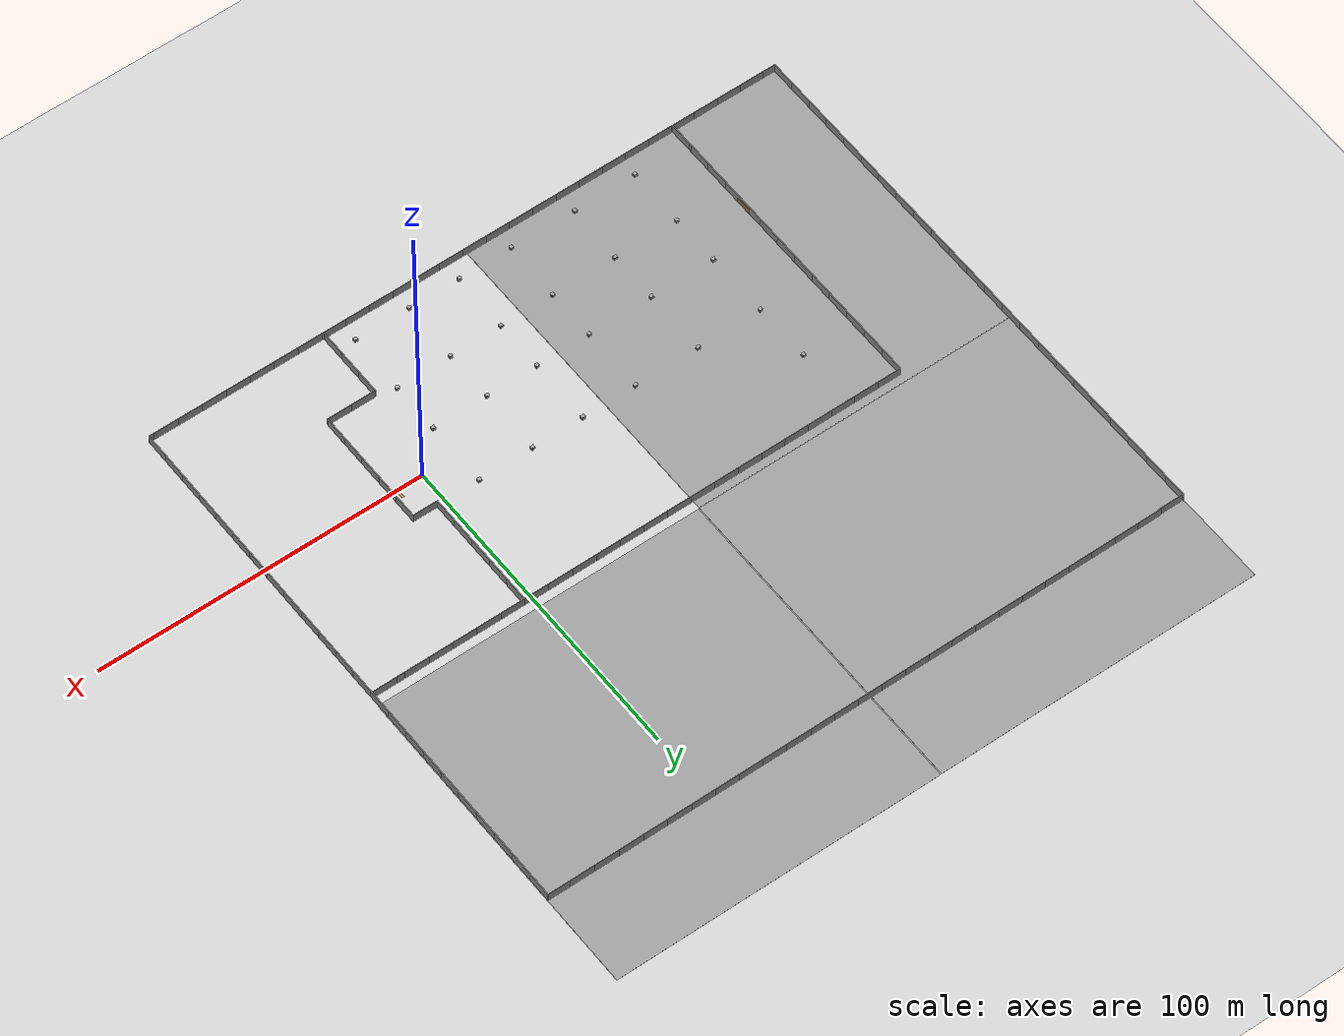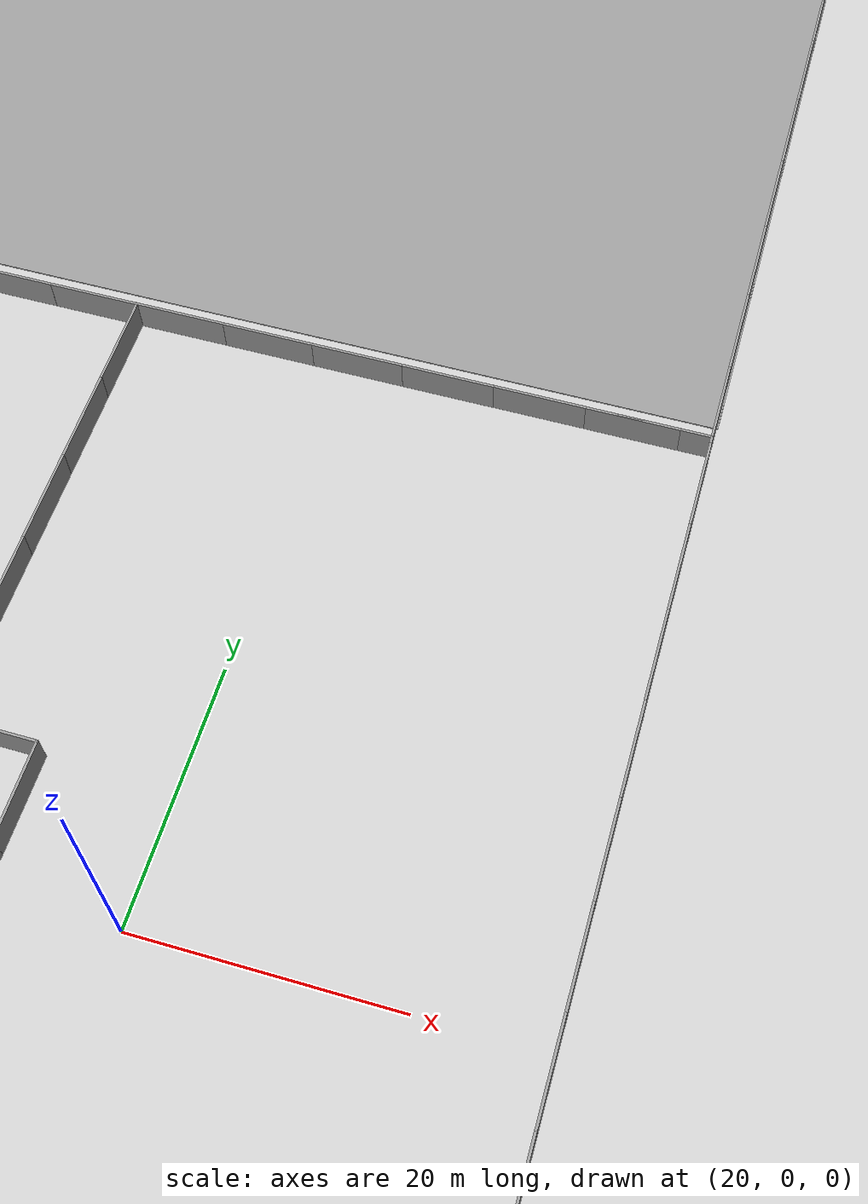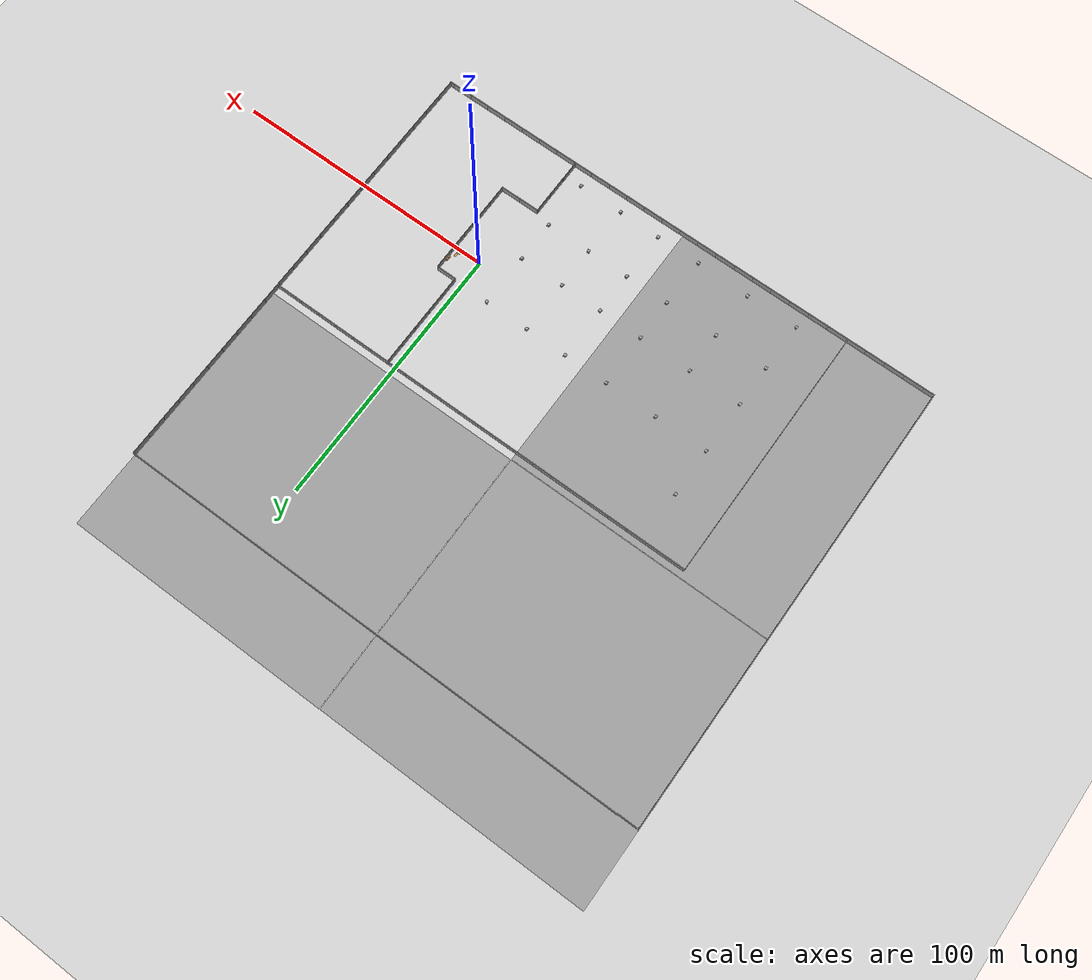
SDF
<sdf version="1.7">
 <world name="default">
  <light name="sun" type="directional">
   <pose>0 0 10 0 -0 0</pose>
   <diffuse>0.8 0.8 0.8 1</diffuse>
   <specular>0.2 0.2 0.2 1</specular>
   <attenuation>
    <range>1000</range>
    <constant>0.9</constant>
    <linear>0.01</linear>
    <quadratic>0.001</quadratic>
   </attenuation>
   <direction>-0.5 0.1 -0.9</direction>
   <spot><inner_angle>0</inner_angle><outer_angle>0</outer_angle><falloff>0</falloff></spot>
  </light>
  <model name="ground_plane">
   <static>1</static>
   <link name="link">
    <collision name="collision">
     <geometry><plane><normal>0 0 1</normal><size>100 100</size></plane></geometry>
     <surface>
      <contact><collide_bitmask>65535</collide_bitmask></contact>
      <friction><ode><mu>100</mu><mu2>50</mu2></ode></friction>
     </surface>
    </collision>
    <visual name="visual">
     <cast_shadows>0</cast_shadows>
     <geometry><plane><normal>0 0 1</normal><size>100 100</size></plane></geometry>
     <material>
      <script><uri>file://media/materials/scripts/gazebo.material</uri><name>Gazebo/Grey</name></script>
     </material>
    </visual>
   </link>
  </model>
  <gravity>0 0 -9.8</gravity>
  <magnetic_field>6e-06 2.3e-05 -4.2e-05</magnetic_field>
  <atmosphere type="adiabatic"/>
  <physics type="ode">
   <max_step_size>0.001</max_step_size>
   <real_time_factor>1</real_time_factor>
   <real_time_update_rate>1000</real_time_update_rate>
  </physics>
  <scene><ambient>0.4 0.4 0.4 1</ambient><background>0.7 0.7 0.7 1</background><shadows>1</shadows></scene>
  <audio><device>default</device></audio>
  <spherical_coordinates>
   <surface_model>EARTH_WGS84</surface_model>
   <latitude_deg>0</latitude_deg>
   <longitude_deg>0</longitude_deg>
   <elevation>0</elevation>
   <heading_deg>0</heading_deg>
  </spherical_coordinates>
  <model name="ground_plane_0">
   <static>1</static>
   <link name="link">
    <collision name="collision">
     <geometry><plane><normal>0 0 1</normal><size>100 100</size></plane></geometry>
     <surface>
      <contact><collide_bitmask>65535</collide_bitmask></contact>
      <friction><ode><mu>100</mu><mu2>50</mu2></ode></friction>
     </surface>
    </collision>
    <visual name="visual">
     <cast_shadows>0</cast_shadows>
     <geometry><plane><normal>0 0 1</normal><size>100 100</size></plane></geometry>
     <material>
      <script><uri>file://media/materials/scripts/gazebo.material</uri><name>Gazebo/Grey</name></script>
     </material>
    </visual>
   </link>
   <pose>0.002609 100.193 0 0 -0 0</pose>
  </model>
  <model name="ground_plane_1">
   <static>1</static>
   <link name="link">
    <collision name="collision">
     <geometry><plane><normal>0 0 1</normal><size>100 100</size></plane></geometry>
     <surface>
      <contact><collide_bitmask>65535</collide_bitmask></contact>
      <friction><ode><mu>100</mu><mu2>50</mu2></ode></friction>
     </surface>
    </collision>
    <visual name="visual">
     <cast_shadows>0</cast_shadows>
     <geometry><plane><normal>0 0 1</normal><size>100 100</size></plane></geometry>
     <material>
      <script><uri>file://media/materials/scripts/gazebo.material</uri><name>Gazebo/Grey</name></script>
     </material>
    </visual>
   </link>
   <pose>-100.275 100.115 0 0 -0 0</pose>
  </model>
  <model name="ground_plane_2">
   <static>1</static>
   <link name="link">
    <collision name="collision">
     <geometry><plane><normal>0 0 1</normal><size>100 100</size></plane></geometry>
     <surface>
      <contact><collide_bitmask>65535</collide_bitmask></contact>
      <friction><ode><mu>100</mu><mu2>50</mu2></ode></friction>
     </surface>
    </collision>
    <visual name="visual">
     <cast_shadows>0</cast_shadows>
     <geometry><plane><normal>0 0 1</normal><size>100 100</size></plane></geometry>
     <material>
      <script><uri>file://media/materials/scripts/gazebo.material</uri><name>Gazebo/Grey</name></script>
     </material>
    </visual>
   </link>
   <pose>-100.275 -0.034671 0 0 -0 0</pose>
  </model>
  <model name="grey_wall_clone">
   <static>1</static>
   <link name="link">
    <pose>0 0 1.4 0 -0 0</pose>
    <collision name="collision"><geometry><box><size>7.5 0.2 2.8</size></box></geometry></collision>
    <visual name="visual">
     <cast_shadows>0</cast_shadows>
     <geometry><box><size>7.5 0.2 2.8</size></box></geometry>
     <material>
      <script>
       <uri>model://grey_wall/materials/scripts</uri>
       <uri>model://grey_wall/materials/textures</uri>
       <name>vrc/grey_wall</name>
      </script>
     </material>
    </visual>
   </link>
   <pose>7.13079 -49.8823 0 0 -0 0</pose>
  </model>
  <model name="grey_wall_clone_0">
   <static>1</static>
   <link name="link">
    <pose>0 0 1.4 0 -0 0</pose>
    <collision name="collision"><geometry><box><size>7.5 0.2 2.8</size></box></geometry></collision>
    <visual name="visual">
     <cast_shadows>0</cast_shadows>
     <geometry><box><size>7.5 0.2 2.8</size></box></geometry>
     <material>
      <script>
       <uri>model://grey_wall/materials/scripts</uri>
       <uri>model://grey_wall/materials/textures</uri>
       <name>vrc/grey_wall</name>
      </script>
     </material>
    </visual>
   </link>
   <pose>-0.374793 -49.8831 0 0 -0 0</pose>
  </model>
  <model name="grey_wall_clone_1">
   <static>1</static>
   <link name="link">
    <pose>0 0 1.4 0 -0 0</pose>
    <collision name="collision"><geometry><box><size>7.5 0.2 2.8</size></box></geometry></collision>
    <visual name="visual">
     <cast_shadows>0</cast_shadows>
     <geometry><box><size>7.5 0.2 2.8</size></box></geometry>
     <material>
      <script>
       <uri>model://grey_wall/materials/scripts</uri>
       <uri>model://grey_wall/materials/textures</uri>
       <name>vrc/grey_wall</name>
      </script>
     </material>
    </visual>
   </link>
   <pose>-7.88033 -49.8844 0 0 -0 0</pose>
  </model>
  <model name="grey_wall_clone_2">
   <static>1</static>
   <link name="link">
    <pose>0 0 1.4 0 -0 0</pose>
    <collision name="collision"><geometry><box><size>7.5 0.2 2.8</size></box></geometry></collision>
    <visual name="visual">
     <cast_shadows>0</cast_shadows>
     <geometry><box><size>7.5 0.2 2.8</size></box></geometry>
     <material>
      <script>
       <uri>model://grey_wall/materials/scripts</uri>
       <uri>model://grey_wall/materials/textures</uri>
       <name>vrc/grey_wall</name>
      </script>
     </material>
    </visual>
   </link>
   <pose>-15.3843 -49.877 0 0 -0 0</pose>
  </model>
  <model name="grey_wall_clone_3">
   <static>1</static>
   <link name="link">
    <pose>0 0 1.4 0 -0 0</pose>
    <collision name="collision"><geometry><box><size>7.5 0.2 2.8</size></box></geometry></collision>
    <visual name="visual">
     <cast_shadows>0</cast_shadows>
     <geometry><box><size>7.5 0.2 2.8</size></box></geometry>
     <material>
      <script>
       <uri>model://grey_wall/materials/scripts</uri>
       <uri>model://grey_wall/materials/textures</uri>
       <name>vrc/grey_wall</name>
      </script>
     </material>
    </visual>
   </link>
   <pose>-22.8836 -49.8847 0 0 -0 0</pose>
  </model>
  <model name="grey_wall_clone_4">
   <static>1</static>
   <link name="link">
    <pose>0 0 1.4 0 -0 0</pose>
    <collision name="collision"><geometry><box><size>7.5 0.2 2.8</size></box></geometry></collision>
    <visual name="visual">
     <cast_shadows>0</cast_shadows>
     <geometry><box><size>7.5 0.2 2.8</size></box></geometry>
     <material>
      <script>
       <uri>model://grey_wall/materials/scripts</uri>
       <uri>model://grey_wall/materials/textures</uri>
       <name>vrc/grey_wall</name>
      </script>
     </material>
    </visual>
   </link>
   <pose>-30.2619 -49.8845 0 0 -0 0</pose>
  </model>
  <model name="grey_wall_clone_5">
   <static>1</static>
   <link name="link">
    <pose>0 0 1.4 0 -0 0</pose>
    <collision name="collision"><geometry><box><size>7.5 0.2 2.8</size></box></geometry></collision>
    <visual name="visual">
     <cast_shadows>0</cast_shadows>
     <geometry><box><size>7.5 0.2 2.8</size></box></geometry>
     <material>
      <script>
       <uri>model://grey_wall/materials/scripts</uri>
       <uri>model://grey_wall/materials/textures</uri>
       <name>vrc/grey_wall</name>
      </script>
     </material>
    </visual>
   </link>
   <pose>-37.6658 -49.8798 0 0 -0 0</pose>
  </model>
  <model name="grey_wall_clone_6">
   <static>1</static>
   <link name="link">
    <pose>0 0 1.4 0 -0 0</pose>
    <collision name="collision"><geometry><box><size>7.5 0.2 2.8</size></box></geometry></collision>
    <visual name="visual">
     <cast_shadows>0</cast_shadows>
     <geometry><box><size>7.5 0.2 2.8</size></box></geometry>
     <material>
      <script>
       <uri>model://grey_wall/materials/scripts</uri>
       <uri>model://grey_wall/materials/textures</uri>
       <name>vrc/grey_wall</name>
      </script>
     </material>
    </visual>
   </link>
   <pose>-45.0649 -49.8818 0 0 -0 0</pose>
  </model>
  <model name="grey_wall_clone_7">
   <static>1</static>
   <link name="link">
    <pose>0 0 1.4 0 -0 0</pose>
    <collision name="collision"><geometry><box><size>7.5 0.2 2.8</size></box></geometry></collision>
    <visual name="visual">
     <cast_shadows>0</cast_shadows>
     <geometry><box><size>7.5 0.2 2.8</size></box></geometry>
     <material>
      <script>
       <uri>model://grey_wall/materials/scripts</uri>
       <uri>model://grey_wall/materials/textures</uri>
       <name>vrc/grey_wall</name>
      </script>
     </material>
    </visual>
   </link>
   <pose>-52.4924 -49.8817 0 0 -0 0</pose>
  </model>
  <model name="grey_wall_clone_8">
   <static>1</static>
   <link name="link">
    <pose>0 0 1.4 0 -0 0</pose>
    <collision name="collision"><geometry><box><size>7.5 0.2 2.8</size></box></geometry></collision>
    <visual name="visual">
     <cast_shadows>0</cast_shadows>
     <geometry><box><size>7.5 0.2 2.8</size></box></geometry>
     <material>
      <script>
       <uri>model://grey_wall/materials/scripts</uri>
       <uri>model://grey_wall/materials/textures</uri>
       <name>vrc/grey_wall</name>
      </script>
     </material>
    </visual>
   </link>
   <pose>-59.9913 -49.8823 0 0 -0 0</pose>
  </model>
  <model name="grey_wall_clone_9">
   <static>1</static>
   <link name="link">
    <pose>0 0 1.4 0 -0 0</pose>
    <collision name="collision"><geometry><box><size>7.5 0.2 2.8</size></box></geometry></collision>
    <visual name="visual">
     <cast_shadows>0</cast_shadows>
     <geometry><box><size>7.5 0.2 2.8</size></box></geometry>
     <material>
      <script>
       <uri>model://grey_wall/materials/scripts</uri>
       <uri>model://grey_wall/materials/textures</uri>
       <name>vrc/grey_wall</name>
      </script>
     </material>
    </visual>
   </link>
   <pose>-67.4862 -49.8731 0 0 -0 0</pose>
  </model>
  <model name="grey_wall_clone_10">
   <static>1</static>
   <link name="link">
    <pose>0 0 1.4 0 -0 0</pose>
    <collision name="collision"><geometry><box><size>7.5 0.2 2.8</size></box></geometry></collision>
    <visual name="visual">
     <cast_shadows>0</cast_shadows>
     <geometry><box><size>7.5 0.2 2.8</size></box></geometry>
     <material>
      <script>
       <uri>model://grey_wall/materials/scripts</uri>
       <uri>model://grey_wall/materials/textures</uri>
       <name>vrc/grey_wall</name>
      </script>
     </material>
    </visual>
   </link>
   <pose>-74.9801 -49.877 0 0 -0 0</pose>
  </model>
  <model name="grey_wall_clone_11">
   <static>1</static>
   <link name="link">
    <pose>0 0 1.4 0 -0 0</pose>
    <collision name="collision"><geometry><box><size>7.5 0.2 2.8</size></box></geometry></collision>
    <visual name="visual">
     <cast_shadows>0</cast_shadows>
     <geometry><box><size>7.5 0.2 2.8</size></box></geometry>
     <material>
      <script>
       <uri>model://grey_wall/materials/scripts</uri>
       <uri>model://grey_wall/materials/textures</uri>
       <name>vrc/grey_wall</name>
      </script>
     </material>
    </visual>
   </link>
   <pose>-82.4353 -49.869 0 0 -0 0</pose>
  </model>
  <model name="grey_wall_clone_12">
   <static>1</static>
   <link name="link">
    <pose>0 0 1.4 0 -0 0</pose>
    <collision name="collision"><geometry><box><size>7.5 0.2 2.8</size></box></geometry></collision>
    <visual name="visual">
     <cast_shadows>0</cast_shadows>
     <geometry><box><size>7.5 0.2 2.8</size></box></geometry>
     <material>
      <script>
       <uri>model://grey_wall/materials/scripts</uri>
       <uri>model://grey_wall/materials/textures</uri>
       <name>vrc/grey_wall</name>
      </script>
     </material>
    </visual>
   </link>
   <pose>-89.9316 -49.8737 0 0 -0 0</pose>
  </model>
  <model name="grey_wall_clone_13">
   <static>1</static>
   <link name="link">
    <pose>0 0 1.4 0 -0 0</pose>
    <collision name="collision"><geometry><box><size>7.5 0.2 2.8</size></box></geometry></collision>
    <visual name="visual">
     <cast_shadows>0</cast_shadows>
     <geometry><box><size>7.5 0.2 2.8</size></box></geometry>
     <material>
      <script>
       <uri>model://grey_wall/materials/scripts</uri>
       <uri>model://grey_wall/materials/textures</uri>
       <name>vrc/grey_wall</name>
      </script>
     </material>
    </visual>
   </link>
   <pose>-97.4162 -49.8717 0 0 -0 0</pose>
  </model>
  <model name="grey_wall_clone_14">
   <static>1</static>
   <link name="link">
    <pose>0 0 1.4 0 -0 0</pose>
    <collision name="collision"><geometry><box><size>7.5 0.2 2.8</size></box></geometry></collision>
    <visual name="visual">
     <cast_shadows>0</cast_shadows>
     <geometry><box><size>7.5 0.2 2.8</size></box></geometry>
     <material>
      <script>
       <uri>model://grey_wall/materials/scripts</uri>
       <uri>model://grey_wall/materials/textures</uri>
       <name>vrc/grey_wall</name>
      </script>
     </material>
    </visual>
   </link>
   <pose>-104.907 -49.8747 0 0 -0 0</pose>
  </model>
  <model name="grey_wall_clone_15">
   <static>1</static>
   <link name="link">
    <pose>0 0 1.4 0 -0 0</pose>
    <collision name="collision"><geometry><box><size>7.5 0.2 2.8</size></box></geometry></collision>
    <visual name="visual">
     <cast_shadows>0</cast_shadows>
     <geometry><box><size>7.5 0.2 2.8</size></box></geometry>
     <material>
      <script>
       <uri>model://grey_wall/materials/scripts</uri>
       <uri>model://grey_wall/materials/textures</uri>
       <name>vrc/grey_wall</name>
      </script>
     </material>
    </visual>
   </link>
   <pose>-112.407 -49.8706 0 0 -0 0</pose>
  </model>
  <model name="grey_wall_clone_16">
   <static>1</static>
   <link name="link">
    <pose>0 0 1.4 0 -0 0</pose>
    <collision name="collision"><geometry><box><size>7.5 0.2 2.8</size></box></geometry></collision>
    <visual name="visual">
     <cast_shadows>0</cast_shadows>
     <geometry><box><size>7.5 0.2 2.8</size></box></geometry>
     <material>
      <script>
       <uri>model://grey_wall/materials/scripts</uri>
       <uri>model://grey_wall/materials/textures</uri>
       <name>vrc/grey_wall</name>
      </script>
     </material>
    </visual>
   </link>
   <pose>-119.879 -49.868 0 0 -0 0</pose>
  </model>
  <model name="grey_wall_clone_17">
   <static>1</static>
   <link name="link">
    <pose>0 0 1.4 0 -0 0</pose>
    <collision name="collision"><geometry><box><size>7.5 0.2 2.8</size></box></geometry></collision>
    <visual name="visual">
     <cast_shadows>0</cast_shadows>
     <geometry><box><size>7.5 0.2 2.8</size></box></geometry>
     <material>
      <script>
       <uri>model://grey_wall/materials/scripts</uri>
       <uri>model://grey_wall/materials/textures</uri>
       <name>vrc/grey_wall</name>
      </script>
     </material>
    </visual>
   </link>
   <pose>-127.376 -49.8696 0 0 -0 0</pose>
  </model>
  <model name="grey_wall_clone_18">
   <static>1</static>
   <link name="link">
    <pose>0 0 1.4 0 -0 0</pose>
    <collision name="collision"><geometry><box><size>7.5 0.2 2.8</size></box></geometry></collision>
    <visual name="visual">
     <cast_shadows>0</cast_shadows>
     <geometry><box><size>7.5 0.2 2.8</size></box></geometry>
     <material>
      <script>
       <uri>model://grey_wall/materials/scripts</uri>
       <uri>model://grey_wall/materials/textures</uri>
       <name>vrc/grey_wall</name>
      </script>
     </material>
    </visual>
   </link>
   <pose>-134.865 -49.8693 0 0 -0 0</pose>
  </model>
  <model name="grey_wall_clone_19">
   <static>1</static>
   <link name="link">
    <pose>0 0 1.4 0 -0 0</pose>
    <collision name="collision"><geometry><box><size>7.5 0.2 2.8</size></box></geometry></collision>
    <visual name="visual">
     <cast_shadows>0</cast_shadows>
     <geometry><box><size>7.5 0.2 2.8</size></box></geometry>
     <material>
      <script>
       <uri>model://grey_wall/materials/scripts</uri>
       <uri>model://grey_wall/materials/textures</uri>
       <name>vrc/grey_wall</name>
      </script>
     </material>
    </visual>
   </link>
   <pose>-142.357 -49.8625 0 0 -0 0</pose>
  </model>
  <model name="grey_wall_clone_20">
   <static>1</static>
   <link name="link">
    <pose>0 0 1.4 0 -0 0</pose>
    <collision name="collision"><geometry><box><size>7.5 0.2 2.8</size></box></geometry></collision>
    <visual name="visual">
     <cast_shadows>0</cast_shadows>
     <geometry><box><size>7.5 0.2 2.8</size></box></geometry>
     <material>
      <script>
       <uri>model://grey_wall/materials/scripts</uri>
       <uri>model://grey_wall/materials/textures</uri>
       <name>vrc/grey_wall</name>
      </script>
     </material>
    </visual>
   </link>
   <pose>-146.458 -49.8642 0 0 -0 0</pose>
  </model>
  <model name="grey_wall_clone_21">
   <static>1</static>
   <link name="link">
    <pose>0 0 1.4 0 -0 0</pose>
    <collision name="collision"><geometry><box><size>7.5 0.2 2.8</size></box></geometry></collision>
    <visual name="visual">
     <cast_shadows>0</cast_shadows>
     <geometry><box><size>7.5 0.2 2.8</size></box></geometry>
     <material>
      <script>
       <uri>model://grey_wall/materials/scripts</uri>
       <uri>model://grey_wall/materials/textures</uri>
       <name>vrc/grey_wall</name>
      </script>
     </material>
    </visual>
   </link>
   <pose>-150.109 -46.212 0 0 -0 1.57</pose>
  </model>
  <model name="grey_wall_clone_21_clone">
   <static>1</static>
   <link name="link">
    <pose>0 0 1.4 0 -0 0</pose>
    <collision name="collision"><geometry><box><size>7.5 0.2 2.8</size></box></geometry></collision>
    <visual name="visual">
     <cast_shadows>0</cast_shadows>
     <geometry><box><size>7.5 0.2 2.8</size></box></geometry>
     <material>
      <script>
       <uri>model://grey_wall/materials/scripts</uri>
       <uri>model://grey_wall/materials/textures</uri>
       <name>vrc/grey_wall</name>
      </script>
     </material>
    </visual>
   </link>
   <pose>-150.111 -38.7432 0 0 -0 1.57</pose>
  </model>
  <model name="grey_wall_clone_21_clone_0">
   <static>1</static>
   <link name="link">
    <pose>0 0 1.4 0 -0 0</pose>
    <collision name="collision"><geometry><box><size>7.5 0.2 2.8</size></box></geometry></collision>
    <visual name="visual">
     <cast_shadows>0</cast_shadows>
     <geometry><box><size>7.5 0.2 2.8</size></box></geometry>
     <material>
      <script>
       <uri>model://grey_wall/materials/scripts</uri>
       <uri>model://grey_wall/materials/textures</uri>
       <name>vrc/grey_wall</name>
      </script>
     </material>
    </visual>
   </link>
   <pose>-150.104 -31.2804 0 0 -0 1.57</pose>
  </model>
  <model name="grey_wall_clone_21_clone_1">
   <static>1</static>
   <link name="link">
    <pose>0 0 1.4 0 -0 0</pose>
    <collision name="collision"><geometry><box><size>7.5 0.2 2.8</size></box></geometry></collision>
    <visual name="visual">
     <cast_shadows>0</cast_shadows>
     <geometry><box><size>7.5 0.2 2.8</size></box></geometry>
     <material>
      <script>
       <uri>model://grey_wall/materials/scripts</uri>
       <uri>model://grey_wall/materials/textures</uri>
       <name>vrc/grey_wall</name>
      </script>
     </material>
    </visual>
   </link>
   <pose>-150.096 -23.8165 0 0 -0 1.57</pose>
  </model>
  <model name="grey_wall_clone_21_clone_2">
   <static>1</static>
   <link name="link">
    <pose>0 0 1.4 0 -0 0</pose>
    <collision name="collision"><geometry><box><size>7.5 0.2 2.8</size></box></geometry></collision>
    <visual name="visual">
     <cast_shadows>0</cast_shadows>
     <geometry><box><size>7.5 0.2 2.8</size></box></geometry>
     <material>
      <script>
       <uri>model://grey_wall/materials/scripts</uri>
       <uri>model://grey_wall/materials/textures</uri>
       <name>vrc/grey_wall</name>
      </script>
     </material>
    </visual>
   </link>
   <pose>-150.091 -16.3673 0 0 -0 1.57</pose>
  </model>
  <model name="grey_wall_clone_21_clone_3">
   <static>1</static>
   <link name="link">
    <pose>0 0 1.4 0 -0 0</pose>
    <collision name="collision"><geometry><box><size>7.5 0.2 2.8</size></box></geometry></collision>
    <visual name="visual">
     <cast_shadows>0</cast_shadows>
     <geometry><box><size>7.5 0.2 2.8</size></box></geometry>
     <material>
      <script>
       <uri>model://grey_wall/materials/scripts</uri>
       <uri>model://grey_wall/materials/textures</uri>
       <name>vrc/grey_wall</name>
      </script>
     </material>
    </visual>
   </link>
   <pose>-150.086 -8.8736 0 0 -0 1.57</pose>
  </model>
  <model name="grey_wall_clone_21_clone_4">
   <static>1</static>
   <link name="link">
    <pose>0 0 1.4 0 -0 0</pose>
    <collision name="collision"><geometry><box><size>7.5 0.2 2.8</size></box></geometry></collision>
    <visual name="visual">
     <cast_shadows>0</cast_shadows>
     <geometry><box><size>7.5 0.2 2.8</size></box></geometry>
     <material>
      <script>
       <uri>model://grey_wall/materials/scripts</uri>
       <uri>model://grey_wall/materials/textures</uri>
       <name>vrc/grey_wall</name>
      </script>
     </material>
    </visual>
   </link>
   <pose>-150.086 -1.38788 0 0 -0 1.57</pose>
  </model>
  <model name="grey_wall_clone_21_clone_5">
   <static>1</static>
   <link name="link">
    <pose>0 0 1.4 0 -0 0</pose>
    <collision name="collision"><geometry><box><size>7.5 0.2 2.8</size></box></geometry></collision>
    <visual name="visual">
     <cast_shadows>0</cast_shadows>
     <geometry><box><size>7.5 0.2 2.8</size></box></geometry>
     <material>
      <script>
       <uri>model://grey_wall/materials/scripts</uri>
       <uri>model://grey_wall/materials/textures</uri>
       <name>vrc/grey_wall</name>
      </script>
     </material>
    </visual>
   </link>
   <pose>-150.077 6.08061 0 0 -0 1.57</pose>
  </model>
  <model name="grey_wall_clone_21_clone_6">
   <static>1</static>
   <link name="link">
    <pose>0 0 1.4 0 -0 0</pose>
    <collision name="collision"><geometry><box><size>7.5 0.2 2.8</size></box></geometry></collision>
    <visual name="visual">
     <cast_shadows>0</cast_shadows>
     <geometry><box><size>7.5 0.2 2.8</size></box></geometry>
     <material>
      <script>
       <uri>model://grey_wall/materials/scripts</uri>
       <uri>model://grey_wall/materials/textures</uri>
       <name>vrc/grey_wall</name>
      </script>
     </material>
    </visual>
   </link>
   <pose>-150.074 13.5681 0 0 -0 1.57</pose>
  </model>
  <model name="grey_wall_clone_21_clone_7">
   <static>1</static>
   <link name="link">
    <pose>0 0 1.4 0 -0 0</pose>
    <collision name="collision"><geometry><box><size>7.5 0.2 2.8</size></box></geometry></collision>
    <visual name="visual">
     <cast_shadows>0</cast_shadows>
     <geometry><box><size>7.5 0.2 2.8</size></box></geometry>
     <material>
      <script>
       <uri>model://grey_wall/materials/scripts</uri>
       <uri>model://grey_wall/materials/textures</uri>
       <name>vrc/grey_wall</name>
      </script>
     </material>
    </visual>
   </link>
   <pose>-150.072 20.9835 0 0 -0 1.57</pose>
  </model>
  <model name="grey_wall_clone_21_clone_8">
   <static>1</static>
   <link name="link">
    <pose>0 0 1.4 0 -0 0</pose>
    <collision name="collision"><geometry><box><size>7.5 0.2 2.8</size></box></geometry></collision>
    <visual name="visual">
     <cast_shadows>0</cast_shadows>
     <geometry><box><size>7.5 0.2 2.8</size></box></geometry>
     <material>
      <script>
       <uri>model://grey_wall/materials/scripts</uri>
       <uri>model://grey_wall/materials/textures</uri>
       <name>vrc/grey_wall</name>
      </script>
     </material>
    </visual>
   </link>
   <pose>-150.068 28.4195 0 0 -0 1.57</pose>
  </model>
  <model name="grey_wall_clone_21_clone_9">
   <static>1</static>
   <link name="link">
    <pose>0 0 1.4 0 -0 0</pose>
    <collision name="collision"><geometry><box><size>7.5 0.2 2.8</size></box></geometry></collision>
    <visual name="visual">
     <cast_shadows>0</cast_shadows>
     <geometry><box><size>7.5 0.2 2.8</size></box></geometry>
     <material>
      <script>
       <uri>model://grey_wall/materials/scripts</uri>
       <uri>model://grey_wall/materials/textures</uri>
       <name>vrc/grey_wall</name>
      </script>
     </material>
    </visual>
   </link>
   <pose>-150.068 35.8569 0 0 -0 1.57</pose>
  </model>
  <model name="grey_wall_clone_21_clone_10">
   <static>1</static>
   <link name="link">
    <pose>0 0 1.4 0 -0 0</pose>
    <collision name="collision"><geometry><box><size>7.5 0.2 2.8</size></box></geometry></collision>
    <visual name="visual">
     <cast_shadows>0</cast_shadows>
     <geometry><box><size>7.5 0.2 2.8</size></box></geometry>
     <material>
      <script>
       <uri>model://grey_wall/materials/scripts</uri>
       <uri>model://grey_wall/materials/textures</uri>
       <name>vrc/grey_wall</name>
      </script>
     </material>
    </visual>
   </link>
   <pose>-150.061 43.3516 0 0 -0 1.57</pose>
  </model>
  <model name="grey_wall_clone_21_clone_11">
   <static>1</static>
   <link name="link">
    <pose>0 0 1.4 0 -0 0</pose>
    <collision name="collision"><geometry><box><size>7.5 0.2 2.8</size></box></geometry></collision>
    <visual name="visual">
     <cast_shadows>0</cast_shadows>
     <geometry><box><size>7.5 0.2 2.8</size></box></geometry>
     <material>
      <script>
       <uri>model://grey_wall/materials/scripts</uri>
       <uri>model://grey_wall/materials/textures</uri>
       <name>vrc/grey_wall</name>
      </script>
     </material>
    </visual>
   </link>
   <pose>-150.056 50.821 0 0 -0 1.57</pose>
  </model>
  <model name="grey_wall_clone_21_clone_12">
   <static>1</static>
   <link name="link">
    <pose>0 0 1.4 0 -0 0</pose>
    <collision name="collision"><geometry><box><size>7.5 0.2 2.8</size></box></geometry></collision>
    <visual name="visual">
     <cast_shadows>0</cast_shadows>
     <geometry><box><size>7.5 0.2 2.8</size></box></geometry>
     <material>
      <script>
       <uri>model://grey_wall/materials/scripts</uri>
       <uri>model://grey_wall/materials/textures</uri>
       <name>vrc/grey_wall</name>
      </script>
     </material>
    </visual>
   </link>
   <pose>-150.051 58.306 0 0 -0 1.57</pose>
  </model>
  <model name="grey_wall_clone_21_clone_13">
   <static>1</static>
   <link name="link">
    <pose>0 0 1.4 0 -0 0</pose>
    <collision name="collision"><geometry><box><size>7.5 0.2 2.8</size></box></geometry></collision>
    <visual name="visual">
     <cast_shadows>0</cast_shadows>
     <geometry><box><size>7.5 0.2 2.8</size></box></geometry>
     <material>
      <script>
       <uri>model://grey_wall/materials/scripts</uri>
       <uri>model://grey_wall/materials/textures</uri>
       <name>vrc/grey_wall</name>
      </script>
     </material>
    </visual>
   </link>
   <pose>-150.053 65.7294 0 0 -0 1.57</pose>
  </model>
  <model name="grey_wall_clone_21_clone_14">
   <static>1</static>
   <link name="link">
    <pose>0 0 1.4 0 -0 0</pose>
    <collision name="collision"><geometry><box><size>7.5 0.2 2.8</size></box></geometry></collision>
    <visual name="visual">
     <cast_shadows>0</cast_shadows>
     <geometry><box><size>7.5 0.2 2.8</size></box></geometry>
     <material>
      <script>
       <uri>model://grey_wall/materials/scripts</uri>
       <uri>model://grey_wall/materials/textures</uri>
       <name>vrc/grey_wall</name>
      </script>
     </material>
    </visual>
   </link>
   <pose>-150.035 73.1423 0 0 -0 1.57</pose>
  </model>
  <model name="grey_wall_clone_21_clone_15">
   <static>1</static>
   <link name="link">
    <pose>0 0 1.4 0 -0 0</pose>
    <collision name="collision"><geometry><box><size>7.5 0.2 2.8</size></box></geometry></collision>
    <visual name="visual">
     <cast_shadows>0</cast_shadows>
     <geometry><box><size>7.5 0.2 2.8</size></box></geometry>
     <material>
      <script>
       <uri>model://grey_wall/materials/scripts</uri>
       <uri>model://grey_wall/materials/textures</uri>
       <name>vrc/grey_wall</name>
      </script>
     </material>
    </visual>
   </link>
   <pose>-150.036 80.6208 0 0 -0 1.57</pose>
  </model>
  <model name="grey_wall_clone_21_clone_16">
   <static>1</static>
   <link name="link">
    <pose>0 0 1.4 0 -0 0</pose>
    <collision name="collision"><geometry><box><size>7.5 0.2 2.8</size></box></geometry></collision>
    <visual name="visual">
     <cast_shadows>0</cast_shadows>
     <geometry><box><size>7.5 0.2 2.8</size></box></geometry>
     <material>
      <script>
       <uri>model://grey_wall/materials/scripts</uri>
       <uri>model://grey_wall/materials/textures</uri>
       <name>vrc/grey_wall</name>
      </script>
     </material>
    </visual>
   </link>
   <pose>-150.032 88.0725 0 0 -0 1.57</pose>
  </model>
  <model name="grey_wall_clone_21_clone_17">
   <static>1</static>
   <link name="link">
    <pose>0 0 1.4 0 -0 0</pose>
    <collision name="collision"><geometry><box><size>7.5 0.2 2.8</size></box></geometry></collision>
    <visual name="visual">
     <cast_shadows>0</cast_shadows>
     <geometry><box><size>7.5 0.2 2.8</size></box></geometry>
     <material>
      <script>
       <uri>model://grey_wall/materials/scripts</uri>
       <uri>model://grey_wall/materials/textures</uri>
       <name>vrc/grey_wall</name>
      </script>
     </material>
    </visual>
   </link>
   <pose>-150.026 95.544 0 0 -0 1.57</pose>
  </model>
  <model name="grey_wall_clone_21_clone_18">
   <static>1</static>
   <link name="link">
    <pose>0 0 1.4 0 -0 0</pose>
    <collision name="collision"><geometry><box><size>7.5 0.2 2.8</size></box></geometry></collision>
    <visual name="visual">
     <cast_shadows>0</cast_shadows>
     <geometry><box><size>7.5 0.2 2.8</size></box></geometry>
     <material>
      <script>
       <uri>model://grey_wall/materials/scripts</uri>
       <uri>model://grey_wall/materials/textures</uri>
       <name>vrc/grey_wall</name>
      </script>
     </material>
    </visual>
   </link>
   <pose>-150.015 103.006 0 0 -0 1.57</pose>
  </model>
  <model name="grey_wall_clone_21_clone_19">
   <static>1</static>
   <link name="link">
    <pose>0 0 1.4 0 -0 0</pose>
    <collision name="collision"><geometry><box><size>7.5 0.2 2.8</size></box></geometry></collision>
    <visual name="visual">
     <cast_shadows>0</cast_shadows>
     <geometry><box><size>7.5 0.2 2.8</size></box></geometry>
     <material>
      <script>
       <uri>model://grey_wall/materials/scripts</uri>
       <uri>model://grey_wall/materials/textures</uri>
       <name>vrc/grey_wall</name>
      </script>
     </material>
    </visual>
   </link>
   <pose>-150.003 110.449 0 0 -0 1.57</pose>
  </model>
  <model name="grey_wall_clone_21_clone_20">
   <static>1</static>
   <link name="link">
    <pose>0 0 1.4 0 -0 0</pose>
    <collision name="collision"><geometry><box><size>7.5 0.2 2.8</size></box></geometry></collision>
    <visual name="visual">
     <cast_shadows>0</cast_shadows>
     <geometry><box><size>7.5 0.2 2.8</size></box></geometry>
     <material>
      <script>
       <uri>model://grey_wall/materials/scripts</uri>
       <uri>model://grey_wall/materials/textures</uri>
       <name>vrc/grey_wall</name>
      </script>
     </material>
    </visual>
   </link>
   <pose>-150.007 117.904 0 0 -0 1.57</pose>
  </model>
  <model name="grey_wall_clone_21_clone_21">
   <static>1</static>
   <link name="link">
    <pose>0 0 1.4 0 -0 0</pose>
    <collision name="collision"><geometry><box><size>7.5 0.2 2.8</size></box></geometry></collision>
    <visual name="visual">
     <cast_shadows>0</cast_shadows>
     <geometry><box><size>7.5 0.2 2.8</size></box></geometry>
     <material>
      <script>
       <uri>model://grey_wall/materials/scripts</uri>
       <uri>model://grey_wall/materials/textures</uri>
       <name>vrc/grey_wall</name>
      </script>
     </material>
    </visual>
   </link>
   <pose>-145.677 121.344 0 0 -0 0</pose>
  </model>
  <model name="grey_wall_clone_21_clone_21_clone">
   <static>1</static>
   <link name="link">
    <pose>0 0 1.4 0 -0 0</pose>
    <collision name="collision"><geometry><box><size>7.5 0.2 2.8</size></box></geometry></collision>
    <visual name="visual">
     <cast_shadows>0</cast_shadows>
     <geometry><box><size>7.5 0.2 2.8</size></box></geometry>
     <material>
      <script>
       <uri>model://grey_wall/materials/scripts</uri>
       <uri>model://grey_wall/materials/textures</uri>
       <name>vrc/grey_wall</name>
      </script>
     </material>
    </visual>
   </link>
   <pose>-138.965 121.554 0 0 -0 0</pose>
  </model>
  <model name="grey_wall_clone_21_clone_21_clone_0">
   <static>1</static>
   <link name="link">
    <pose>0 0 1.4 0 -0 0</pose>
    <collision name="collision"><geometry><box><size>7.5 0.2 2.8</size></box></geometry></collision>
    <visual name="visual">
     <cast_shadows>0</cast_shadows>
     <geometry><box><size>7.5 0.2 2.8</size></box></geometry>
     <material>
      <script>
       <uri>model://grey_wall/materials/scripts</uri>
       <uri>model://grey_wall/materials/textures</uri>
       <name>vrc/grey_wall</name>
      </script>
     </material>
    </visual>
   </link>
   <pose>-131.474 121.559 0 0 -0 0</pose>
  </model>
  <model name="grey_wall_clone_21_clone_21_clone_1">
   <static>1</static>
   <link name="link">
    <pose>0 0 1.4 0 -0 0</pose>
    <collision name="collision"><geometry><box><size>7.5 0.2 2.8</size></box></geometry></collision>
    <visual name="visual">
     <cast_shadows>0</cast_shadows>
     <geometry><box><size>7.5 0.2 2.8</size></box></geometry>
     <material>
      <script>
       <uri>model://grey_wall/materials/scripts</uri>
       <uri>model://grey_wall/materials/textures</uri>
       <name>vrc/grey_wall</name>
      </script>
     </material>
    </visual>
   </link>
   <pose>-124.004 121.564 0 0 -0 0</pose>
  </model>
  <model name="grey_wall_clone_21_clone_21_clone_2">
   <static>1</static>
   <link name="link">
    <pose>0 0 1.4 0 -0 0</pose>
    <collision name="collision"><geometry><box><size>7.5 0.2 2.8</size></box></geometry></collision>
    <visual name="visual">
     <cast_shadows>0</cast_shadows>
     <geometry><box><size>7.5 0.2 2.8</size></box></geometry>
     <material>
      <script>
       <uri>model://grey_wall/materials/scripts</uri>
       <uri>model://grey_wall/materials/textures</uri>
       <name>vrc/grey_wall</name>
      </script>
     </material>
    </visual>
   </link>
   <pose>-116.614 121.564 0 0 -0 0</pose>
  </model>
  <model name="grey_wall_clone_21_clone_21_clone_3">
   <static>1</static>
   <link name="link">
    <pose>0 0 1.4 0 -0 0</pose>
    <collision name="collision"><geometry><box><size>7.5 0.2 2.8</size></box></geometry></collision>
    <visual name="visual">
     <cast_shadows>0</cast_shadows>
     <geometry><box><size>7.5 0.2 2.8</size></box></geometry>
     <material>
      <script>
       <uri>model://grey_wall/materials/scripts</uri>
       <uri>model://grey_wall/materials/textures</uri>
       <name>vrc/grey_wall</name>
      </script>
     </material>
    </visual>
   </link>
   <pose>-109.14 121.563 0 0 -0 0</pose>
  </model>
  <model name="grey_wall_clone_21_clone_21_clone_4">
   <static>1</static>
   <link name="link">
    <pose>0 0 1.4 0 -0 0</pose>
    <collision name="collision"><geometry><box><size>7.5 0.2 2.8</size></box></geometry></collision>
    <visual name="visual">
     <cast_shadows>0</cast_shadows>
     <geometry><box><size>7.5 0.2 2.8</size></box></geometry>
     <material>
      <script>
       <uri>model://grey_wall/materials/scripts</uri>
       <uri>model://grey_wall/materials/textures</uri>
       <name>vrc/grey_wall</name>
      </script>
     </material>
    </visual>
   </link>
   <pose>-101.642 121.569 0 0 -0 0</pose>
  </model>
  <model name="grey_wall_clone_21_clone_21_clone_5">
   <static>1</static>
   <link name="link">
    <pose>0 0 1.4 0 -0 0</pose>
    <collision name="collision"><geometry><box><size>7.5 0.2 2.8</size></box></geometry></collision>
    <visual name="visual">
     <cast_shadows>0</cast_shadows>
     <geometry><box><size>7.5 0.2 2.8</size></box></geometry>
     <material>
      <script>
       <uri>model://grey_wall/materials/scripts</uri>
       <uri>model://grey_wall/materials/textures</uri>
       <name>vrc/grey_wall</name>
      </script>
     </material>
    </visual>
   </link>
   <pose>-94.2065 121.581 0 0 -0 0</pose>
  </model>
  <model name="grey_wall_clone_21_clone_21_clone_6">
   <static>1</static>
   <link name="link">
    <pose>0 0 1.4 0 -0 0</pose>
    <collision name="collision"><geometry><box><size>7.5 0.2 2.8</size></box></geometry></collision>
    <visual name="visual">
     <cast_shadows>0</cast_shadows>
     <geometry><box><size>7.5 0.2 2.8</size></box></geometry>
     <material>
      <script>
       <uri>model://grey_wall/materials/scripts</uri>
       <uri>model://grey_wall/materials/textures</uri>
       <name>vrc/grey_wall</name>
      </script>
     </material>
    </visual>
   </link>
   <pose>-86.7332 121.59 0 0 -0 0</pose>
  </model>
  <model name="grey_wall_clone_21_clone_21_clone_7">
   <static>1</static>
   <link name="link">
    <pose>0 0 1.4 0 -0 0</pose>
    <collision name="collision"><geometry><box><size>7.5 0.2 2.8</size></box></geometry></collision>
    <visual name="visual">
     <cast_shadows>0</cast_shadows>
     <geometry><box><size>7.5 0.2 2.8</size></box></geometry>
     <material>
      <script>
       <uri>model://grey_wall/materials/scripts</uri>
       <uri>model://grey_wall/materials/textures</uri>
       <name>vrc/grey_wall</name>
      </script>
     </material>
    </visual>
   </link>
   <pose>-79.2923 121.595 0 0 -0 0</pose>
  </model>
  <model name="grey_wall_clone_21_clone_21_clone_8">
   <static>1</static>
   <link name="link">
    <pose>0 0 1.4 0 -0 0</pose>
    <collision name="collision"><geometry><box><size>7.5 0.2 2.8</size></box></geometry></collision>
    <visual name="visual">
     <cast_shadows>0</cast_shadows>
     <geometry><box><size>7.5 0.2 2.8</size></box></geometry>
     <material>
      <script>
       <uri>model://grey_wall/materials/scripts</uri>
       <uri>model://grey_wall/materials/textures</uri>
       <name>vrc/grey_wall</name>
      </script>
     </material>
    </visual>
   </link>
   <pose>-71.929 121.602 0 0 -0 0</pose>
  </model>
  <model name="grey_wall_clone_21_clone_21_clone_9">
   <static>1</static>
   <link name="link">
    <pose>0 0 1.4 0 -0 0</pose>
    <collision name="collision"><geometry><box><size>7.5 0.2 2.8</size></box></geometry></collision>
    <visual name="visual">
     <cast_shadows>0</cast_shadows>
     <geometry><box><size>7.5 0.2 2.8</size></box></geometry>
     <material>
      <script>
       <uri>model://grey_wall/materials/scripts</uri>
       <uri>model://grey_wall/materials/textures</uri>
       <name>vrc/grey_wall</name>
      </script>
     </material>
    </visual>
   </link>
   <pose>-64.5064 121.602 0 0 -0 0</pose>
  </model>
  <model name="grey_wall_clone_21_clone_21_clone_10">
   <static>1</static>
   <link name="link">
    <pose>0 0 1.4 0 -0 0</pose>
    <collision name="collision"><geometry><box><size>7.5 0.2 2.8</size></box></geometry></collision>
    <visual name="visual">
     <cast_shadows>0</cast_shadows>
     <geometry><box><size>7.5 0.2 2.8</size></box></geometry>
     <material>
      <script>
       <uri>model://grey_wall/materials/scripts</uri>
       <uri>model://grey_wall/materials/textures</uri>
       <name>vrc/grey_wall</name>
      </script>
     </material>
    </visual>
   </link>
   <pose>-57.1247 121.608 0 0 -0 0</pose>
  </model>
  <model name="grey_wall_clone_21_clone_21_clone_11">
   <static>1</static>
   <link name="link">
    <pose>0 0 1.4 0 -0 0</pose>
    <collision name="collision"><geometry><box><size>7.5 0.2 2.8</size></box></geometry></collision>
    <visual name="visual">
     <cast_shadows>0</cast_shadows>
     <geometry><box><size>7.5 0.2 2.8</size></box></geometry>
     <material>
      <script>
       <uri>model://grey_wall/materials/scripts</uri>
       <uri>model://grey_wall/materials/textures</uri>
       <name>vrc/grey_wall</name>
      </script>
     </material>
    </visual>
   </link>
   <pose>-49.6689 121.608 0 0 -0 0</pose>
  </model>
  <model name="grey_wall_clone_21_clone_21_clone_12">
   <static>1</static>
   <link name="link">
    <pose>0 0 1.4 0 -0 0</pose>
    <collision name="collision"><geometry><box><size>7.5 0.2 2.8</size></box></geometry></collision>
    <visual name="visual">
     <cast_shadows>0</cast_shadows>
     <geometry><box><size>7.5 0.2 2.8</size></box></geometry>
     <material>
      <script>
       <uri>model://grey_wall/materials/scripts</uri>
       <uri>model://grey_wall/materials/textures</uri>
       <name>vrc/grey_wall</name>
      </script>
     </material>
    </visual>
   </link>
   <pose>-42.214 121.614 0 0 -0 0</pose>
  </model>
  <model name="grey_wall_clone_21_clone_21_clone_13">
   <static>1</static>
   <link name="link">
    <pose>0 0 1.4 0 -0 0</pose>
    <collision name="collision"><geometry><box><size>7.5 0.2 2.8</size></box></geometry></collision>
    <visual name="visual">
     <cast_shadows>0</cast_shadows>
     <geometry><box><size>7.5 0.2 2.8</size></box></geometry>
     <material>
      <script>
       <uri>model://grey_wall/materials/scripts</uri>
       <uri>model://grey_wall/materials/textures</uri>
       <name>vrc/grey_wall</name>
      </script>
     </material>
    </visual>
   </link>
   <pose>-34.7998 121.616 0 0 -0 0</pose>
  </model>
  <model name="grey_wall_clone_21_clone_21_clone_14">
   <static>1</static>
   <link name="link">
    <pose>0 0 1.4 0 -0 0</pose>
    <collision name="collision"><geometry><box><size>7.5 0.2 2.8</size></box></geometry></collision>
    <visual name="visual">
     <cast_shadows>0</cast_shadows>
     <geometry><box><size>7.5 0.2 2.8</size></box></geometry>
     <material>
      <script>
       <uri>model://grey_wall/materials/scripts</uri>
       <uri>model://grey_wall/materials/textures</uri>
       <name>vrc/grey_wall</name>
      </script>
     </material>
    </visual>
   </link>
   <pose>-27.3968 121.621 0 0 -0 0</pose>
  </model>
  <model name="grey_wall_clone_21_clone_21_clone_15">
   <static>1</static>
   <link name="link">
    <pose>0 0 1.4 0 -0 0</pose>
    <collision name="collision"><geometry><box><size>7.5 0.2 2.8</size></box></geometry></collision>
    <visual name="visual">
     <cast_shadows>0</cast_shadows>
     <geometry><box><size>7.5 0.2 2.8</size></box></geometry>
     <material>
      <script>
       <uri>model://grey_wall/materials/scripts</uri>
       <uri>model://grey_wall/materials/textures</uri>
       <name>vrc/grey_wall</name>
      </script>
     </material>
    </visual>
   </link>
   <pose>-19.9142 121.625 0 0 -0 0</pose>
  </model>
  <model name="grey_wall_clone_21_clone_21_clone_16">
   <static>1</static>
   <link name="link">
    <pose>0 0 1.4 0 -0 0</pose>
    <collision name="collision"><geometry><box><size>7.5 0.2 2.8</size></box></geometry></collision>
    <visual name="visual">
     <cast_shadows>0</cast_shadows>
     <geometry><box><size>7.5 0.2 2.8</size></box></geometry>
     <material>
      <script>
       <uri>model://grey_wall/materials/scripts</uri>
       <uri>model://grey_wall/materials/textures</uri>
       <name>vrc/grey_wall</name>
      </script>
     </material>
    </visual>
   </link>
   <pose>-12.5105 121.626 0 0 -0 0</pose>
  </model>
  <model name="grey_wall_clone_21_clone_21_clone_17">
   <static>1</static>
   <link name="link">
    <pose>0 0 1.4 0 -0 0</pose>
    <collision name="collision"><geometry><box><size>7.5 0.2 2.8</size></box></geometry></collision>
    <visual name="visual">
     <cast_shadows>0</cast_shadows>
     <geometry><box><size>7.5 0.2 2.8</size></box></geometry>
     <material>
      <script>
       <uri>model://grey_wall/materials/scripts</uri>
       <uri>model://grey_wall/materials/textures</uri>
       <name>vrc/grey_wall</name>
      </script>
     </material>
    </visual>
   </link>
   <pose>-5.09047 121.63 0 0 -0 0</pose>
  </model>
  <model name="grey_wall_clone_21_clone_21_clone_18">
   <static>1</static>
   <link name="link">
    <pose>0 0 1.4 0 -0 0</pose>
    <collision name="collision"><geometry><box><size>7.5 0.2 2.8</size></box></geometry></collision>
    <visual name="visual">
     <cast_shadows>0</cast_shadows>
     <geometry><box><size>7.5 0.2 2.8</size></box></geometry>
     <material>
      <script>
       <uri>model://grey_wall/materials/scripts</uri>
       <uri>model://grey_wall/materials/textures</uri>
       <name>vrc/grey_wall</name>
      </script>
     </material>
    </visual>
   </link>
   <pose>2.23805 121.637 0 0 -0 0</pose>
  </model>
  <model name="grey_wall_clone_21_clone_21_clone_19">
   <static>1</static>
   <link name="link">
    <pose>0 0 1.4 0 -0 0</pose>
    <collision name="collision"><geometry><box><size>7.5 0.2 2.8</size></box></geometry></collision>
    <visual name="visual">
     <cast_shadows>0</cast_shadows>
     <geometry><box><size>7.5 0.2 2.8</size></box></geometry>
     <material>
      <script>
       <uri>model://grey_wall/materials/scripts</uri>
       <uri>model://grey_wall/materials/textures</uri>
       <name>vrc/grey_wall</name>
      </script>
     </material>
    </visual>
   </link>
   <pose>9.66218 121.639 0 0 -0 0</pose>
  </model>
  <model name="grey_wall_clone_21_clone_21_clone_20">
   <static>1</static>
   <link name="link">
    <pose>0 0 1.4 0 -0 0</pose>
    <collision name="collision"><geometry><box><size>7.5 0.2 2.8</size></box></geometry></collision>
    <visual name="visual">
     <cast_shadows>0</cast_shadows>
     <geometry><box><size>7.5 0.2 2.8</size></box></geometry>
     <material>
      <script>
       <uri>model://grey_wall/materials/scripts</uri>
       <uri>model://grey_wall/materials/textures</uri>
       <name>vrc/grey_wall</name>
      </script>
     </material>
    </visual>
   </link>
   <pose>17.0328 121.638 0 0 -0 0</pose>
  </model>
  <model name="grey_wall_clone_21_clone_21_clone_21">
   <static>1</static>
   <link name="link">
    <pose>0 0 1.4 0 -0 0</pose>
    <collision name="collision"><geometry><box><size>7.5 0.2 2.8</size></box></geometry></collision>
    <visual name="visual">
     <cast_shadows>0</cast_shadows>
     <geometry><box><size>7.5 0.2 2.8</size></box></geometry>
     <material>
      <script>
       <uri>model://grey_wall/materials/scripts</uri>
       <uri>model://grey_wall/materials/textures</uri>
       <name>vrc/grey_wall</name>
      </script>
     </material>
    </visual>
   </link>
   <pose>24.475 121.644 0 0 -0 0</pose>
  </model>
  <model name="grey_wall_clone_21_clone_21_clone_22">
   <static>1</static>
   <link name="link">
    <pose>0 0 1.4 0 -0 0</pose>
    <collision name="collision"><geometry><box><size>7.5 0.2 2.8</size></box></geometry></collision>
    <visual name="visual">
     <cast_shadows>0</cast_shadows>
     <geometry><box><size>7.5 0.2 2.8</size></box></geometry>
     <material>
      <script>
       <uri>model://grey_wall/materials/scripts</uri>
       <uri>model://grey_wall/materials/textures</uri>
       <name>vrc/grey_wall</name>
      </script>
     </material>
    </visual>
   </link>
   <pose>31.9378 121.656 0 0 -0 0</pose>
  </model>
  <model name="grey_wall_clone_21_clone_21_clone_23">
   <static>1</static>
   <link name="link">
    <pose>0 0 1.4 0 -0 0</pose>
    <collision name="collision"><geometry><box><size>7.5 0.2 2.8</size></box></geometry></collision>
    <visual name="visual">
     <cast_shadows>0</cast_shadows>
     <geometry><box><size>7.5 0.2 2.8</size></box></geometry>
     <material>
      <script>
       <uri>model://grey_wall/materials/scripts</uri>
       <uri>model://grey_wall/materials/textures</uri>
       <name>vrc/grey_wall</name>
      </script>
     </material>
    </visual>
   </link>
   <pose>39.3665 121.653 0 0 -0 0</pose>
  </model>
  <model name="grey_wall_clone_21_clone_21_clone_24">
   <static>1</static>
   <link name="link">
    <pose>0 0 1.4 0 -0 0</pose>
    <collision name="collision"><geometry><box><size>7.5 0.2 2.8</size></box></geometry></collision>
    <visual name="visual">
     <cast_shadows>0</cast_shadows>
     <geometry><box><size>7.5 0.2 2.8</size></box></geometry>
     <material>
      <script>
       <uri>model://grey_wall/materials/scripts</uri>
       <uri>model://grey_wall/materials/textures</uri>
       <name>vrc/grey_wall</name>
      </script>
     </material>
    </visual>
   </link>
   <pose>46.1929 121.652 0 0 -0 0</pose>
  </model>
  <model name="grey_wall_clone_21_clone_20_clone">
   <static>1</static>
   <link name="link">
    <pose>0 0 1.4 0 -0 0</pose>
    <collision name="collision"><geometry><box><size>7.5 0.2 2.8</size></box></geometry></collision>
    <visual name="visual">
     <cast_shadows>0</cast_shadows>
     <geometry><box><size>7.5 0.2 2.8</size></box></geometry>
     <material>
      <script>
       <uri>model://grey_wall/materials/scripts</uri>
       <uri>model://grey_wall/materials/textures</uri>
       <name>vrc/grey_wall</name>
      </script>
     </material>
    </visual>
   </link>
   <pose>49.8458 117.894 0 0 -0 1.57</pose>
  </model>
  <model name="grey_wall_clone_21_clone_20_clone_0">
   <static>1</static>
   <link name="link">
    <pose>0 0 1.4 0 -0 0</pose>
    <collision name="collision"><geometry><box><size>7.5 0.2 2.8</size></box></geometry></collision>
    <visual name="visual">
     <cast_shadows>0</cast_shadows>
     <geometry><box><size>7.5 0.2 2.8</size></box></geometry>
     <material>
      <script>
       <uri>model://grey_wall/materials/scripts</uri>
       <uri>model://grey_wall/materials/textures</uri>
       <name>vrc/grey_wall</name>
      </script>
     </material>
    </visual>
   </link>
   <pose>49.8421 110.417 0 0 -0 1.57</pose>
  </model>
  <model name="grey_wall_clone_21_clone_20_clone_1">
   <static>1</static>
   <link name="link">
    <pose>0 0 1.4 0 -0 0</pose>
    <collision name="collision"><geometry><box><size>7.5 0.2 2.8</size></box></geometry></collision>
    <visual name="visual">
     <cast_shadows>0</cast_shadows>
     <geometry><box><size>7.5 0.2 2.8</size></box></geometry>
     <material>
      <script>
       <uri>model://grey_wall/materials/scripts</uri>
       <uri>model://grey_wall/materials/textures</uri>
       <name>vrc/grey_wall</name>
      </script>
     </material>
    </visual>
   </link>
   <pose>49.8335 102.935 0 0 -0 1.57</pose>
  </model>
  <model name="grey_wall_clone_21_clone_20_clone_2">
   <static>1</static>
   <link name="link">
    <pose>0 0 1.4 0 -0 0</pose>
    <collision name="collision"><geometry><box><size>7.5 0.2 2.8</size></box></geometry></collision>
    <visual name="visual">
     <cast_shadows>0</cast_shadows>
     <geometry><box><size>7.5 0.2 2.8</size></box></geometry>
     <material>
      <script>
       <uri>model://grey_wall/materials/scripts</uri>
       <uri>model://grey_wall/materials/textures</uri>
       <name>vrc/grey_wall</name>
      </script>
     </material>
    </visual>
   </link>
   <pose>49.8257 95.4892 0 0 -0 1.57</pose>
  </model>
  <model name="grey_wall_clone_21_clone_20_clone_3">
   <static>1</static>
   <link name="link">
    <pose>0 0 1.4 0 -0 0</pose>
    <collision name="collision"><geometry><box><size>7.5 0.2 2.8</size></box></geometry></collision>
    <visual name="visual">
     <cast_shadows>0</cast_shadows>
     <geometry><box><size>7.5 0.2 2.8</size></box></geometry>
     <material>
      <script>
       <uri>model://grey_wall/materials/scripts</uri>
       <uri>model://grey_wall/materials/textures</uri>
       <name>vrc/grey_wall</name>
      </script>
     </material>
    </visual>
   </link>
   <pose>49.8177 87.9912 0 0 -0 1.57</pose>
  </model>
  <model name="grey_wall_clone_21_clone_20_clone_4">
   <static>1</static>
   <link name="link">
    <pose>0 0 1.4 0 -0 0</pose>
    <collision name="collision"><geometry><box><size>7.5 0.2 2.8</size></box></geometry></collision>
    <visual name="visual">
     <cast_shadows>0</cast_shadows>
     <geometry><box><size>7.5 0.2 2.8</size></box></geometry>
     <material>
      <script>
       <uri>model://grey_wall/materials/scripts</uri>
       <uri>model://grey_wall/materials/textures</uri>
       <name>vrc/grey_wall</name>
      </script>
     </material>
    </visual>
   </link>
   <pose>49.8117 80.5511 0 0 -0 1.57</pose>
  </model>
  <model name="grey_wall_clone_21_clone_20_clone_5">
   <static>1</static>
   <link name="link">
    <pose>0 0 1.4 0 -0 0</pose>
    <collision name="collision"><geometry><box><size>7.5 0.2 2.8</size></box></geometry></collision>
    <visual name="visual">
     <cast_shadows>0</cast_shadows>
     <geometry><box><size>7.5 0.2 2.8</size></box></geometry>
     <material>
      <script>
       <uri>model://grey_wall/materials/scripts</uri>
       <uri>model://grey_wall/materials/textures</uri>
       <name>vrc/grey_wall</name>
      </script>
     </material>
    </visual>
   </link>
   <pose>49.8001 73.0636 0 0 -0 1.57</pose>
  </model>
  <model name="grey_wall_clone_21_clone_20_clone_6">
   <static>1</static>
   <link name="link">
    <pose>0 0 1.4 0 -0 0</pose>
    <collision name="collision"><geometry><box><size>7.5 0.2 2.8</size></box></geometry></collision>
    <visual name="visual">
     <cast_shadows>0</cast_shadows>
     <geometry><box><size>7.5 0.2 2.8</size></box></geometry>
     <material>
      <script>
       <uri>model://grey_wall/materials/scripts</uri>
       <uri>model://grey_wall/materials/textures</uri>
       <name>vrc/grey_wall</name>
      </script>
     </material>
    </visual>
   </link>
   <pose>49.7987 65.5811 0 0 -0 1.57</pose>
  </model>
  <model name="grey_wall_clone_21_clone_20_clone_7">
   <static>1</static>
   <link name="link">
    <pose>0 0 1.4 0 -0 0</pose>
    <collision name="collision"><geometry><box><size>7.5 0.2 2.8</size></box></geometry></collision>
    <visual name="visual">
     <cast_shadows>0</cast_shadows>
     <geometry><box><size>7.5 0.2 2.8</size></box></geometry>
     <material>
      <script>
       <uri>model://grey_wall/materials/scripts</uri>
       <uri>model://grey_wall/materials/textures</uri>
       <name>vrc/grey_wall</name>
      </script>
     </material>
    </visual>
   </link>
   <pose>49.7903 58.1117 0 0 -0 1.57</pose>
  </model>
  <model name="grey_wall_clone_21_clone_20_clone_8">
   <static>1</static>
   <link name="link">
    <pose>0 0 1.4 0 -0 0</pose>
    <collision name="collision"><geometry><box><size>7.5 0.2 2.8</size></box></geometry></collision>
    <visual name="visual">
     <cast_shadows>0</cast_shadows>
     <geometry><box><size>7.5 0.2 2.8</size></box></geometry>
     <material>
      <script>
       <uri>model://grey_wall/materials/scripts</uri>
       <uri>model://grey_wall/materials/textures</uri>
       <name>vrc/grey_wall</name>
      </script>
     </material>
    </visual>
   </link>
   <pose>49.781 50.6517 0 0 -0 1.57</pose>
  </model>
  <model name="grey_wall_clone_21_clone_20_clone_9">
   <static>1</static>
   <link name="link">
    <pose>0 0 1.4 0 -0 0</pose>
    <collision name="collision"><geometry><box><size>7.5 0.2 2.8</size></box></geometry></collision>
    <visual name="visual">
     <cast_shadows>0</cast_shadows>
     <geometry><box><size>7.5 0.2 2.8</size></box></geometry>
     <material>
      <script>
       <uri>model://grey_wall/materials/scripts</uri>
       <uri>model://grey_wall/materials/textures</uri>
       <name>vrc/grey_wall</name>
      </script>
     </material>
    </visual>
   </link>
   <pose>49.7846 43.1803 0 0 -0 1.57</pose>
  </model>
  <model name="grey_wall_clone_21_clone_20_clone_10">
   <static>1</static>
   <link name="link">
    <pose>0 0 1.4 0 -0 0</pose>
    <collision name="collision"><geometry><box><size>7.5 0.2 2.8</size></box></geometry></collision>
    <visual name="visual">
     <cast_shadows>0</cast_shadows>
     <geometry><box><size>7.5 0.2 2.8</size></box></geometry>
     <material>
      <script>
       <uri>model://grey_wall/materials/scripts</uri>
       <uri>model://grey_wall/materials/textures</uri>
       <name>vrc/grey_wall</name>
      </script>
     </material>
    </visual>
   </link>
   <pose>49.7753 35.7603 0 0 -0 1.57</pose>
  </model>
  <model name="grey_wall_clone_21_clone_20_clone_11">
   <static>1</static>
   <link name="link">
    <pose>0 0 1.4 0 -0 0</pose>
    <collision name="collision"><geometry><box><size>7.5 0.2 2.8</size></box></geometry></collision>
    <visual name="visual">
     <cast_shadows>0</cast_shadows>
     <geometry><box><size>7.5 0.2 2.8</size></box></geometry>
     <material>
      <script>
       <uri>model://grey_wall/materials/scripts</uri>
       <uri>model://grey_wall/materials/textures</uri>
       <name>vrc/grey_wall</name>
      </script>
     </material>
    </visual>
   </link>
   <pose>49.7674 28.3584 0 0 -0 1.57</pose>
  </model>
  <model name="grey_wall_clone_21_clone_20_clone_12">
   <static>1</static>
   <link name="link">
    <pose>0 0 1.4 0 -0 0</pose>
    <collision name="collision"><geometry><box><size>7.5 0.2 2.8</size></box></geometry></collision>
    <visual name="visual">
     <cast_shadows>0</cast_shadows>
     <geometry><box><size>7.5 0.2 2.8</size></box></geometry>
     <material>
      <script>
       <uri>model://grey_wall/materials/scripts</uri>
       <uri>model://grey_wall/materials/textures</uri>
       <name>vrc/grey_wall</name>
      </script>
     </material>
    </visual>
   </link>
   <pose>49.776 20.8614 0 0 -0 1.57</pose>
  </model>
  <model name="grey_wall_clone_21_clone_20_clone_13">
   <static>1</static>
   <link name="link">
    <pose>0 0 1.4 0 -0 0</pose>
    <collision name="collision"><geometry><box><size>7.5 0.2 2.8</size></box></geometry></collision>
    <visual name="visual">
     <cast_shadows>0</cast_shadows>
     <geometry><box><size>7.5 0.2 2.8</size></box></geometry>
     <material>
      <script>
       <uri>model://grey_wall/materials/scripts</uri>
       <uri>model://grey_wall/materials/textures</uri>
       <name>vrc/grey_wall</name>
      </script>
     </material>
    </visual>
   </link>
   <pose>49.7689 13.383 0 0 -0 1.57</pose>
  </model>
  <model name="grey_wall_clone_21_clone_20_clone_14">
   <static>1</static>
   <link name="link">
    <pose>0 0 1.4 0 -0 0</pose>
    <collision name="collision"><geometry><box><size>7.5 0.2 2.8</size></box></geometry></collision>
    <visual name="visual">
     <cast_shadows>0</cast_shadows>
     <geometry><box><size>7.5 0.2 2.8</size></box></geometry>
     <material>
      <script>
       <uri>model://grey_wall/materials/scripts</uri>
       <uri>model://grey_wall/materials/textures</uri>
       <name>vrc/grey_wall</name>
      </script>
     </material>
    </visual>
   </link>
   <pose>49.7614 5.89332 0 0 -0 1.57</pose>
  </model>
  <model name="grey_wall_clone_21_clone_20_clone_15">
   <static>1</static>
   <link name="link">
    <pose>0 0 1.4 0 -0 0</pose>
    <collision name="collision"><geometry><box><size>7.5 0.2 2.8</size></box></geometry></collision>
    <visual name="visual">
     <cast_shadows>0</cast_shadows>
     <geometry><box><size>7.5 0.2 2.8</size></box></geometry>
     <material>
      <script>
       <uri>model://grey_wall/materials/scripts</uri>
       <uri>model://grey_wall/materials/textures</uri>
       <name>vrc/grey_wall</name>
      </script>
     </material>
    </visual>
   </link>
   <pose>49.7545 -1.60418 0 0 -0 1.57</pose>
  </model>
  <model name="grey_wall_clone_21_clone_20_clone_16">
   <static>1</static>
   <link name="link">
    <pose>0 0 1.4 0 -0 0</pose>
    <collision name="collision"><geometry><box><size>7.5 0.2 2.8</size></box></geometry></collision>
    <visual name="visual">
     <cast_shadows>0</cast_shadows>
     <geometry><box><size>7.5 0.2 2.8</size></box></geometry>
     <material>
      <script>
       <uri>model://grey_wall/materials/scripts</uri>
       <uri>model://grey_wall/materials/textures</uri>
       <name>vrc/grey_wall</name>
      </script>
     </material>
    </visual>
   </link>
   <pose>49.7485 -9.06367 0 0 -0 1.57</pose>
  </model>
  <model name="grey_wall_clone_21_clone_20_clone_17">
   <static>1</static>
   <link name="link">
    <pose>0 0 1.4 0 -0 0</pose>
    <collision name="collision"><geometry><box><size>7.5 0.2 2.8</size></box></geometry></collision>
    <visual name="visual">
     <cast_shadows>0</cast_shadows>
     <geometry><box><size>7.5 0.2 2.8</size></box></geometry>
     <material>
      <script>
       <uri>model://grey_wall/materials/scripts</uri>
       <uri>model://grey_wall/materials/textures</uri>
       <name>vrc/grey_wall</name>
      </script>
     </material>
    </visual>
   </link>
   <pose>49.7355 -16.5323 0 0 -0 1.57</pose>
  </model>
  <model name="grey_wall_clone_21_clone_20_clone_18">
   <static>1</static>
   <link name="link">
    <pose>0 0 1.4 0 -0 0</pose>
    <collision name="collision"><geometry><box><size>7.5 0.2 2.8</size></box></geometry></collision>
    <visual name="visual">
     <cast_shadows>0</cast_shadows>
     <geometry><box><size>7.5 0.2 2.8</size></box></geometry>
     <material>
      <script>
       <uri>model://grey_wall/materials/scripts</uri>
       <uri>model://grey_wall/materials/textures</uri>
       <name>vrc/grey_wall</name>
      </script>
     </material>
    </visual>
   </link>
   <pose>49.7352 -23.9046 0 0 -0 1.57</pose>
  </model>
  <model name="grey_wall_clone_21_clone_20_clone_19">
   <static>1</static>
   <link name="link">
    <pose>0 0 1.4 0 -0 0</pose>
    <collision name="collision"><geometry><box><size>7.5 0.2 2.8</size></box></geometry></collision>
    <visual name="visual">
     <cast_shadows>0</cast_shadows>
     <geometry><box><size>7.5 0.2 2.8</size></box></geometry>
     <material>
      <script>
       <uri>model://grey_wall/materials/scripts</uri>
       <uri>model://grey_wall/materials/textures</uri>
       <name>vrc/grey_wall</name>
      </script>
     </material>
    </visual>
   </link>
   <pose>49.734 -31.3808 0 0 -0 1.57</pose>
  </model>
  <model name="grey_wall_clone_21_clone_20_clone_20">
   <static>1</static>
   <link name="link">
    <pose>0 0 1.4 0 -0 0</pose>
    <collision name="collision"><geometry><box><size>7.5 0.2 2.8</size></box></geometry></collision>
    <visual name="visual">
     <cast_shadows>0</cast_shadows>
     <geometry><box><size>7.5 0.2 2.8</size></box></geometry>
     <material>
      <script>
       <uri>model://grey_wall/materials/scripts</uri>
       <uri>model://grey_wall/materials/textures</uri>
       <name>vrc/grey_wall</name>
      </script>
     </material>
    </visual>
   </link>
   <pose>49.7216 -38.8579 0 0 -0 1.57</pose>
  </model>
  <model name="grey_wall_clone_21_clone_20_clone_21">
   <static>1</static>
   <link name="link">
    <pose>0 0 1.4 0 -0 0</pose>
    <collision name="collision"><geometry><box><size>7.5 0.2 2.8</size></box></geometry></collision>
    <visual name="visual">
     <cast_shadows>0</cast_shadows>
     <geometry><box><size>7.5 0.2 2.8</size></box></geometry>
     <material>
      <script>
       <uri>model://grey_wall/materials/scripts</uri>
       <uri>model://grey_wall/materials/textures</uri>
       <name>vrc/grey_wall</name>
      </script>
     </material>
    </visual>
   </link>
   <pose>49.7104 -46.1719 0 0 -0 1.57</pose>
  </model>
  <model name="grey_wall_clone_clone">
   <static>1</static>
   <link name="link">
    <pose>0 0 1.4 0 -0 0</pose>
    <collision name="collision"><geometry><box><size>7.5 0.2 2.8</size></box></geometry></collision>
    <visual name="visual">
     <cast_shadows>0</cast_shadows>
     <geometry><box><size>7.5 0.2 2.8</size></box></geometry>
     <material>
      <script>
       <uri>model://grey_wall/materials/scripts</uri>
       <uri>model://grey_wall/materials/textures</uri>
       <name>vrc/grey_wall</name>
      </script>
     </material>
    </visual>
   </link>
   <pose>14.6278 -49.8878 0 0 -0 0</pose>
  </model>
  <model name="grey_wall_clone_clone_0">
   <static>1</static>
   <link name="link">
    <pose>0 0 1.4 0 -0 0</pose>
    <collision name="collision"><geometry><box><size>7.5 0.2 2.8</size></box></geometry></collision>
    <visual name="visual">
     <cast_shadows>0</cast_shadows>
     <geometry><box><size>7.5 0.2 2.8</size></box></geometry>
     <material>
      <script>
       <uri>model://grey_wall/materials/scripts</uri>
       <uri>model://grey_wall/materials/textures</uri>
       <name>vrc/grey_wall</name>
      </script>
     </material>
    </visual>
   </link>
   <pose>22.0975 -49.8885 0 0 -0 0</pose>
  </model>
  <model name="grey_wall_clone_clone_1">
   <static>1</static>
   <link name="link">
    <pose>0 0 1.4 0 -0 0</pose>
    <collision name="collision"><geometry><box><size>7.5 0.2 2.8</size></box></geometry></collision>
    <visual name="visual">
     <cast_shadows>0</cast_shadows>
     <geometry><box><size>7.5 0.2 2.8</size></box></geometry>
     <material>
      <script>
       <uri>model://grey_wall/materials/scripts</uri>
       <uri>model://grey_wall/materials/textures</uri>
       <name>vrc/grey_wall</name>
      </script>
     </material>
    </visual>
   </link>
   <pose>29.56 -49.8861 0 0 -0 0</pose>
  </model>
  <model name="grey_wall_clone_clone_2">
   <static>1</static>
   <link name="link">
    <pose>0 0 1.4 0 -0 0</pose>
    <collision name="collision"><geometry><box><size>7.5 0.2 2.8</size></box></geometry></collision>
    <visual name="visual">
     <cast_shadows>0</cast_shadows>
     <geometry><box><size>7.5 0.2 2.8</size></box></geometry>
     <material>
      <script>
       <uri>model://grey_wall/materials/scripts</uri>
       <uri>model://grey_wall/materials/textures</uri>
       <name>vrc/grey_wall</name>
      </script>
     </material>
    </visual>
   </link>
   <pose>37.0546 -49.8861 0 0 -0 0</pose>
  </model>
  <model name="grey_wall_clone_clone_3">
   <static>1</static>
   <link name="link">
    <pose>0 0 1.4 0 -0 0</pose>
    <collision name="collision"><geometry><box><size>7.5 0.2 2.8</size></box></geometry></collision>
    <visual name="visual">
     <cast_shadows>0</cast_shadows>
     <geometry><box><size>7.5 0.2 2.8</size></box></geometry>
     <material>
      <script>
       <uri>model://grey_wall/materials/scripts</uri>
       <uri>model://grey_wall/materials/textures</uri>
       <name>vrc/grey_wall</name>
      </script>
     </material>
    </visual>
   </link>
   <pose>44.538 -49.8866 0 0 -0 0</pose>
  </model>
  <model name="grey_wall_clone_clone_4">
   <static>1</static>
   <link name="link">
    <pose>0 0 1.4 0 -0 0</pose>
    <collision name="collision"><geometry><box><size>7.5 0.2 2.8</size></box></geometry></collision>
    <visual name="visual">
     <cast_shadows>0</cast_shadows>
     <geometry><box><size>7.5 0.2 2.8</size></box></geometry>
     <material>
      <script>
       <uri>model://grey_wall/materials/scripts</uri>
       <uri>model://grey_wall/materials/textures</uri>
       <name>vrc/grey_wall</name>
      </script>
     </material>
    </visual>
   </link>
   <pose>46.0661 -49.8918 0 0 -0 0</pose>
  </model>
  <model name="grey_wall_clone_clone_5">
   <static>1</static>
   <link name="link">
    <pose>0 0 1.4 0 -0 0</pose>
    <collision name="collision"><geometry><box><size>7.5 0.2 2.8</size></box></geometry></collision>
    <visual name="visual">
     <cast_shadows>0</cast_shadows>
     <geometry><box><size>7.5 0.2 2.8</size></box></geometry>
     <material>
      <script>
       <uri>model://grey_wall/materials/scripts</uri>
       <uri>model://grey_wall/materials/textures</uri>
       <name>vrc/grey_wall</name>
      </script>
     </material>
    </visual>
   </link>
   <pose>6.48493 10.1452 0 0 -0 0</pose>
  </model>
  <model name="grey_wall_clone_21_clone_20_clone_13_clone">
   <static>1</static>
   <link name="link">
    <pose>0 0 1.4 0 -0 0</pose>
    <collision name="collision"><geometry><box><size>7.5 0.2 2.8</size></box></geometry></collision>
    <visual name="visual">
     <cast_shadows>0</cast_shadows>
     <geometry><box><size>7.5 0.2 2.8</size></box></geometry>
     <material>
      <script>
       <uri>model://grey_wall/materials/scripts</uri>
       <uri>model://grey_wall/materials/textures</uri>
       <name>vrc/grey_wall</name>
      </script>
     </material>
    </visual>
   </link>
   <pose>10.1575 6.47546 0 0 -0 1.57</pose>
  </model>
  <model name="grey_wall_clone_21_clone_20_clone_13_clone_0">
   <static>1</static>
   <link name="link">
    <pose>0 0 1.4 0 -0 0</pose>
    <collision name="collision"><geometry><box><size>7.5 0.2 2.8</size></box></geometry></collision>
    <visual name="visual">
     <cast_shadows>0</cast_shadows>
     <geometry><box><size>7.5 0.2 2.8</size></box></geometry>
     <material>
      <script>
       <uri>model://grey_wall/materials/scripts</uri>
       <uri>model://grey_wall/materials/textures</uri>
       <name>vrc/grey_wall</name>
      </script>
     </material>
    </visual>
   </link>
   <pose>10.1533 -1.00076 0 0 -0 1.57</pose>
  </model>
  <model name="grey_wall_clone_21_clone_20_clone_13_clone_1">
   <static>1</static>
   <link name="link">
    <pose>0 0 1.4 0 -0 0</pose>
    <collision name="collision"><geometry><box><size>7.5 0.2 2.8</size></box></geometry></collision>
    <visual name="visual">
     <cast_shadows>0</cast_shadows>
     <geometry><box><size>7.5 0.2 2.8</size></box></geometry>
     <material>
      <script>
       <uri>model://grey_wall/materials/scripts</uri>
       <uri>model://grey_wall/materials/textures</uri>
       <name>vrc/grey_wall</name>
      </script>
     </material>
    </visual>
   </link>
   <pose>10.1452 -8.50424 0 0 -0 1.57</pose>
  </model>
  <model name="grey_wall_clone_21_clone_20_clone_13_clone_2">
   <static>1</static>
   <link name="link">
    <pose>0 0 1.4 0 -0 0</pose>
    <collision name="collision"><geometry><box><size>7.5 0.2 2.8</size></box></geometry></collision>
    <visual name="visual">
     <cast_shadows>0</cast_shadows>
     <geometry><box><size>7.5 0.2 2.8</size></box></geometry>
     <material>
      <script>
       <uri>model://grey_wall/materials/scripts</uri>
       <uri>model://grey_wall/materials/textures</uri>
       <name>vrc/grey_wall</name>
      </script>
     </material>
    </visual>
   </link>
   <pose>10.1381 -15.9861 0 0 -0 1.57</pose>
  </model>
  <model name="grey_wall_clone_21_clone_20_clone_13_clone_3">
   <static>1</static>
   <link name="link">
    <pose>0 0 1.4 0 -0 0</pose>
    <collision name="collision"><geometry><box><size>7.5 0.2 2.8</size></box></geometry></collision>
    <visual name="visual">
     <cast_shadows>0</cast_shadows>
     <geometry><box><size>7.5 0.2 2.8</size></box></geometry>
     <material>
      <script>
       <uri>model://grey_wall/materials/scripts</uri>
       <uri>model://grey_wall/materials/textures</uri>
       <name>vrc/grey_wall</name>
      </script>
     </material>
    </visual>
   </link>
   <pose>10.1348 -23.447 0 0 -0 1.57</pose>
  </model>
  <model name="grey_wall_clone_clone_5_clone">
   <static>1</static>
   <link name="link">
    <pose>0 0 1.4 0 -0 0</pose>
    <collision name="collision"><geometry><box><size>7.5 0.2 2.8</size></box></geometry></collision>
    <visual name="visual">
     <cast_shadows>0</cast_shadows>
     <geometry><box><size>7.5 0.2 2.8</size></box></geometry>
     <material>
      <script>
       <uri>model://grey_wall/materials/scripts</uri>
       <uri>model://grey_wall/materials/textures</uri>
       <name>vrc/grey_wall</name>
      </script>
     </material>
    </visual>
   </link>
   <pose>6.49638 -27.1102 0 0 -0 0</pose>
  </model>
  <model name="grey_wall_clone_clone_5_clone_0">
   <static>1</static>
   <link name="link">
    <pose>0 0 1.4 0 -0 0</pose>
    <collision name="collision"><geometry><box><size>7.5 0.2 2.8</size></box></geometry></collision>
    <visual name="visual">
     <cast_shadows>0</cast_shadows>
     <geometry><box><size>7.5 0.2 2.8</size></box></geometry>
     <material>
      <script>
       <uri>model://grey_wall/materials/scripts</uri>
       <uri>model://grey_wall/materials/textures</uri>
       <name>vrc/grey_wall</name>
      </script>
     </material>
    </visual>
   </link>
   <pose>-0.969636 -27.1078 0 0 -0 0</pose>
  </model>
  <model name="grey_wall_clone_21_clone_20_clone_13_clone_3_clone">
   <static>1</static>
   <link name="link">
    <pose>0 0 1.4 0 -0 0</pose>
    <collision name="collision"><geometry><box><size>7.5 0.2 2.8</size></box></geometry></collision>
    <visual name="visual">
     <cast_shadows>0</cast_shadows>
     <geometry><box><size>7.5 0.2 2.8</size></box></geometry>
     <material>
      <script>
       <uri>model://grey_wall/materials/scripts</uri>
       <uri>model://grey_wall/materials/textures</uri>
       <name>vrc/grey_wall</name>
      </script>
     </material>
    </visual>
   </link>
   <pose>-4.79323 -30.7579 0 0 -0 1.57</pose>
  </model>
  <model name="grey_wall_clone_21_clone_20_clone_13_clone_3_clone_0">
   <static>1</static>
   <link name="link">
    <pose>0 0 1.4 0 -0 0</pose>
    <collision name="collision"><geometry><box><size>7.5 0.2 2.8</size></box></geometry></collision>
    <visual name="visual">
     <cast_shadows>0</cast_shadows>
     <geometry><box><size>7.5 0.2 2.8</size></box></geometry>
     <material>
      <script>
       <uri>model://grey_wall/materials/scripts</uri>
       <uri>model://grey_wall/materials/textures</uri>
       <name>vrc/grey_wall</name>
      </script>
     </material>
    </visual>
   </link>
   <pose>-4.8016 -38.2646 0 0 -0 1.57</pose>
  </model>
  <model name="grey_wall_clone_21_clone_20_clone_13_clone_3_clone_1">
   <static>1</static>
   <link name="link">
    <pose>0 0 1.4 0 -0 0</pose>
    <collision name="collision"><geometry><box><size>7.5 0.2 2.8</size></box></geometry></collision>
    <visual name="visual">
     <cast_shadows>0</cast_shadows>
     <geometry><box><size>7.5 0.2 2.8</size></box></geometry>
     <material>
      <script>
       <uri>model://grey_wall/materials/scripts</uri>
       <uri>model://grey_wall/materials/textures</uri>
       <name>vrc/grey_wall</name>
      </script>
     </material>
    </visual>
   </link>
   <pose>-4.81761 -45.7125 0 0 -0 1.57</pose>
  </model>
  <model name="grey_wall_clone_21_clone_20_clone_13_clone_3_clone_2">
   <static>1</static>
   <link name="link">
    <pose>0 0 1.4 0 -0 0</pose>
    <collision name="collision"><geometry><box><size>7.5 0.2 2.8</size></box></geometry></collision>
    <visual name="visual">
     <cast_shadows>0</cast_shadows>
     <geometry><box><size>7.5 0.2 2.8</size></box></geometry>
     <material>
      <script>
       <uri>model://grey_wall/materials/scripts</uri>
       <uri>model://grey_wall/materials/textures</uri>
       <name>vrc/grey_wall</name>
      </script>
     </material>
    </visual>
   </link>
   <pose>-4.82476 -46.2342 0 0 -0 1.57</pose>
  </model>
  <model name="grey_wall_clone_21_clone_20_clone_13_clone_3_clone_3">
   <static>1</static>
   <link name="link">
    <pose>0 0 1.4 0 -0 0</pose>
    <collision name="collision"><geometry><box><size>7.5 0.2 2.8</size></box></geometry></collision>
    <visual name="visual">
     <cast_shadows>0</cast_shadows>
     <geometry><box><size>7.5 0.2 2.8</size></box></geometry>
     <material>
      <script>
       <uri>model://grey_wall/materials/scripts</uri>
       <uri>model://grey_wall/materials/textures</uri>
       <name>vrc/grey_wall</name>
      </script>
     </material>
    </visual>
   </link>
   <pose>2.64459 13.7844 0 0 -0 1.57</pose>
  </model>
  <model name="grey_wall_clone_21_clone_20_clone_13_clone_3_clone_4">
   <static>1</static>
   <link name="link">
    <pose>0 0 1.4 0 -0 0</pose>
    <collision name="collision"><geometry><box><size>7.5 0.2 2.8</size></box></geometry></collision>
    <visual name="visual">
     <cast_shadows>0</cast_shadows>
     <geometry><box><size>7.5 0.2 2.8</size></box></geometry>
     <material>
      <script>
       <uri>model://grey_wall/materials/scripts</uri>
       <uri>model://grey_wall/materials/textures</uri>
       <name>vrc/grey_wall</name>
      </script>
     </material>
    </visual>
   </link>
   <pose>2.64823 21.2582 0 0 -0 1.57</pose>
  </model>
  <model name="grey_wall_clone_21_clone_20_clone_13_clone_3_clone_5">
   <static>1</static>
   <link name="link">
    <pose>0 0 1.4 0 -0 0</pose>
    <collision name="collision"><geometry><box><size>7.5 0.2 2.8</size></box></geometry></collision>
    <visual name="visual">
     <cast_shadows>0</cast_shadows>
     <geometry><box><size>7.5 0.2 2.8</size></box></geometry>
     <material>
      <script>
       <uri>model://grey_wall/materials/scripts</uri>
       <uri>model://grey_wall/materials/textures</uri>
       <name>vrc/grey_wall</name>
      </script>
     </material>
    </visual>
   </link>
   <pose>2.65433 28.7306 0 0 -0 1.57</pose>
  </model>
  <model name="grey_wall_clone_21_clone_20_clone_13_clone_3_clone_6">
   <static>1</static>
   <link name="link">
    <pose>0 0 1.4 0 -0 0</pose>
    <collision name="collision"><geometry><box><size>7.5 0.2 2.8</size></box></geometry></collision>
    <visual name="visual">
     <cast_shadows>0</cast_shadows>
     <geometry><box><size>7.5 0.2 2.8</size></box></geometry>
     <material>
      <script>
       <uri>model://grey_wall/materials/scripts</uri>
       <uri>model://grey_wall/materials/textures</uri>
       <name>vrc/grey_wall</name>
      </script>
     </material>
    </visual>
   </link>
   <pose>2.66098 36.2088 0 0 -0 1.57</pose>
  </model>
  <model name="grey_wall_clone_21_clone_20_clone_13_clone_3_clone_7">
   <static>1</static>
   <link name="link">
    <pose>0 0 1.4 0 -0 0</pose>
    <collision name="collision"><geometry><box><size>7.5 0.2 2.8</size></box></geometry></collision>
    <visual name="visual">
     <cast_shadows>0</cast_shadows>
     <geometry><box><size>7.5 0.2 2.8</size></box></geometry>
     <material>
      <script>
       <uri>model://grey_wall/materials/scripts</uri>
       <uri>model://grey_wall/materials/textures</uri>
       <name>vrc/grey_wall</name>
      </script>
     </material>
    </visual>
   </link>
   <pose>2.66664 43.6957 0 0 -0 1.57</pose>
  </model>
  <model name="grey_wall_clone_clone_5_clone_clone">
   <static>1</static>
   <link name="link">
    <pose>0 0 1.4 0 -0 0</pose>
    <collision name="collision"><geometry><box><size>7.5 0.2 2.8</size></box></geometry></collision>
    <visual name="visual">
     <cast_shadows>0</cast_shadows>
     <geometry><box><size>7.5 0.2 2.8</size></box></geometry>
     <material>
      <script>
       <uri>model://grey_wall/materials/scripts</uri>
       <uri>model://grey_wall/materials/textures</uri>
       <name>vrc/grey_wall</name>
      </script>
     </material>
    </visual>
   </link>
   <pose>6.31799 47.5177 0 0 -0 0</pose>
  </model>
  <model name="grey_wall_clone_clone_5_clone_clone_0">
   <static>1</static>
   <link name="link">
    <pose>0 0 1.4 0 -0 0</pose>
    <collision name="collision"><geometry><box><size>7.5 0.2 2.8</size></box></geometry></collision>
    <visual name="visual">
     <cast_shadows>0</cast_shadows>
     <geometry><box><size>7.5 0.2 2.8</size></box></geometry>
     <material>
      <script>
       <uri>model://grey_wall/materials/scripts</uri>
       <uri>model://grey_wall/materials/textures</uri>
       <name>vrc/grey_wall</name>
      </script>
     </material>
    </visual>
   </link>
   <pose>13.7763 47.5141 0 0 -0 0</pose>
  </model>
  <model name="grey_wall_clone_clone_5_clone_clone_1">
   <static>1</static>
   <link name="link">
    <pose>0 0 1.4 0 -0 0</pose>
    <collision name="collision"><geometry><box><size>7.5 0.2 2.8</size></box></geometry></collision>
    <visual name="visual">
     <cast_shadows>0</cast_shadows>
     <geometry><box><size>7.5 0.2 2.8</size></box></geometry>
     <material>
      <script>
       <uri>model://grey_wall/materials/scripts</uri>
       <uri>model://grey_wall/materials/textures</uri>
       <name>vrc/grey_wall</name>
      </script>
     </material>
    </visual>
   </link>
   <pose>21.2459 47.5085 0 0 -0 0</pose>
  </model>
  <model name="grey_wall_clone_clone_5_clone_clone_2">
   <static>1</static>
   <link name="link">
    <pose>0 0 1.4 0 -0 0</pose>
    <collision name="collision"><geometry><box><size>7.5 0.2 2.8</size></box></geometry></collision>
    <visual name="visual">
     <cast_shadows>0</cast_shadows>
     <geometry><box><size>7.5 0.2 2.8</size></box></geometry>
     <material>
      <script>
       <uri>model://grey_wall/materials/scripts</uri>
       <uri>model://grey_wall/materials/textures</uri>
       <name>vrc/grey_wall</name>
      </script>
     </material>
    </visual>
   </link>
   <pose>28.6972 47.5084 0 0 -0 0</pose>
  </model>
  <model name="grey_wall_clone_clone_5_clone_clone_3">
   <static>1</static>
   <link name="link">
    <pose>0 0 1.4 0 -0 0</pose>
    <collision name="collision"><geometry><box><size>7.5 0.2 2.8</size></box></geometry></collision>
    <visual name="visual">
     <cast_shadows>0</cast_shadows>
     <geometry><box><size>7.5 0.2 2.8</size></box></geometry>
     <material>
      <script>
       <uri>model://grey_wall/materials/scripts</uri>
       <uri>model://grey_wall/materials/textures</uri>
       <name>vrc/grey_wall</name>
      </script>
     </material>
    </visual>
   </link>
   <pose>36.1214 47.5187 0 0 -0 0</pose>
  </model>
  <model name="grey_wall_clone_clone_5_clone_clone_4">
   <static>1</static>
   <link name="link">
    <pose>0 0 1.4 0 -0 0</pose>
    <collision name="collision"><geometry><box><size>7.5 0.2 2.8</size></box></geometry></collision>
    <visual name="visual">
     <cast_shadows>0</cast_shadows>
     <geometry><box><size>7.5 0.2 2.8</size></box></geometry>
     <material>
      <script>
       <uri>model://grey_wall/materials/scripts</uri>
       <uri>model://grey_wall/materials/textures</uri>
       <name>vrc/grey_wall</name>
      </script>
     </material>
    </visual>
   </link>
   <pose>43.5705 47.5133 0 0 -0 0</pose>
  </model>
  <model name="grey_wall_clone_clone_5_clone_clone_5">
   <static>1</static>
   <link name="link">
    <pose>0 0 1.4 0 -0 0</pose>
    <collision name="collision"><geometry><box><size>7.5 0.2 2.8</size></box></geometry></collision>
    <visual name="visual">
     <cast_shadows>0</cast_shadows>
     <geometry><box><size>7.5 0.2 2.8</size></box></geometry>
     <material>
      <script>
       <uri>model://grey_wall/materials/scripts</uri>
       <uri>model://grey_wall/materials/textures</uri>
       <name>vrc/grey_wall</name>
      </script>
     </material>
    </visual>
   </link>
   <pose>46.1045 47.515 0 0 -0 0</pose>
  </model>
  <model name="table_clone">
   <static>1</static>
   <link name="link">
    <collision name="surface">
     <pose>0 0 1 0 -0 0</pose>
     <geometry><box><size>1.5 0.8 0.03</size></box></geometry>
     <surface><friction><ode><mu>0.6</mu><mu2>0.6</mu2></ode></friction></surface>
    </collision>
    <visual name="visual1">
     <pose>0 0 1 0 -0 0</pose>
     <geometry><box><size>1.5 0.8 0.03</size></box></geometry>
     <material>
      <script><uri>file://media/materials/scripts/gazebo.material</uri><name>Gazebo/Wood</name></script>
     </material>
    </visual>
    <collision name="front_left_leg">
     <pose>0.68 0.38 0.5 0 -0 0</pose>
     <geometry><cylinder><radius>0.02</radius><length>1</length></cylinder></geometry>
    </collision>
    <visual name="front_left_leg">
     <pose>0.68 0.38 0.5 0 -0 0</pose>
     <geometry><cylinder><radius>0.02</radius><length>1</length></cylinder></geometry>
     <material>
      <script><uri>file://media/materials/scripts/gazebo.material</uri><name>Gazebo/Grey</name></script>
     </material>
    </visual>
    <collision name="front_right_leg">
     <pose>0.68 -0.38 0.5 0 -0 0</pose>
     <geometry><cylinder><radius>0.02</radius><length>1</length></cylinder></geometry>
    </collision>
    <visual name="front_right_leg">
     <pose>0.68 -0.38 0.5 0 -0 0</pose>
     <geometry><cylinder><radius>0.02</radius><length>1</length></cylinder></geometry>
     <material>
      <script><uri>file://media/materials/scripts/gazebo.material</uri><name>Gazebo/Grey</name></script>
     </material>
    </visual>
    <collision name="back_right_leg">
     <pose>-0.68 -0.38 0.5 0 -0 0</pose>
     <geometry><cylinder><radius>0.02</radius><length>1</length></cylinder></geometry>
    </collision>
    <visual name="back_right_leg">
     <pose>-0.68 -0.38 0.5 0 -0 0</pose>
     <geometry><cylinder><radius>0.02</radius><length>1</length></cylinder></geometry>
     <material>
      <script><uri>file://media/materials/scripts/gazebo.material</uri><name>Gazebo/Grey</name></script>
     </material>
    </visual>
    <collision name="back_left_leg">
     <pose>-0.68 0.38 0.5 0 -0 0</pose>
     <geometry><cylinder><radius>0.02</radius><length>1</length></cylinder></geometry>
    </collision>
    <visual name="back_left_leg">
     <pose>-0.68 0.38 0.5 0 -0 0</pose>
     <geometry><cylinder><radius>0.02</radius><length>1</length></cylinder></geometry>
     <material>
      <script><uri>file://media/materials/scripts/gazebo.material</uri><name>Gazebo/Grey</name></script>
     </material>
    </visual>
   </link>
   <pose>8.24796 2.34857 0 0 0 -1.60074</pose>
  </model>
  <model name="table_clone_0">
   <static>1</static>
   <link name="link">
    <collision name="surface">
     <pose>0 0 1 0 -0 0</pose>
     <geometry><box><size>1.5 0.8 0.03</size></box></geometry>
     <surface><friction><ode><mu>0.6</mu><mu2>0.6</mu2></ode></friction></surface>
    </collision>
    <visual name="visual1">
     <pose>0 0 1 0 -0 0</pose>
     <geometry><box><size>1.5 0.8 0.03</size></box></geometry>
     <material>
      <script><uri>file://media/materials/scripts/gazebo.material</uri><name>Gazebo/Wood</name></script>
     </material>
    </visual>
    <collision name="front_left_leg">
     <pose>0.68 0.38 0.5 0 -0 0</pose>
     <geometry><cylinder><radius>0.02</radius><length>1</length></cylinder></geometry>
    </collision>
    <visual name="front_left_leg">
     <pose>0.68 0.38 0.5 0 -0 0</pose>
     <geometry><cylinder><radius>0.02</radius><length>1</length></cylinder></geometry>
     <material>
      <script><uri>file://media/materials/scripts/gazebo.material</uri><name>Gazebo/Grey</name></script>
     </material>
    </visual>
    <collision name="front_right_leg">
     <pose>0.68 -0.38 0.5 0 -0 0</pose>
     <geometry><cylinder><radius>0.02</radius><length>1</length></cylinder></geometry>
    </collision>
    <visual name="front_right_leg">
     <pose>0.68 -0.38 0.5 0 -0 0</pose>
     <geometry><cylinder><radius>0.02</radius><length>1</length></cylinder></geometry>
     <material>
      <script><uri>file://media/materials/scripts/gazebo.material</uri><name>Gazebo/Grey</name></script>
     </material>
    </visual>
    <collision name="back_right_leg">
     <pose>-0.68 -0.38 0.5 0 -0 0</pose>
     <geometry><cylinder><radius>0.02</radius><length>1</length></cylinder></geometry>
    </collision>
    <visual name="back_right_leg">
     <pose>-0.68 -0.38 0.5 0 -0 0</pose>
     <geometry><cylinder><radius>0.02</radius><length>1</length></cylinder></geometry>
     <material>
      <script><uri>file://media/materials/scripts/gazebo.material</uri><name>Gazebo/Grey</name></script>
     </material>
    </visual>
    <collision name="back_left_leg">
     <pose>-0.68 0.38 0.5 0 -0 0</pose>
     <geometry><cylinder><radius>0.02</radius><length>1</length></cylinder></geometry>
    </collision>
    <visual name="back_left_leg">
     <pose>-0.68 0.38 0.5 0 -0 0</pose>
     <geometry><cylinder><radius>0.02</radius><length>1</length></cylinder></geometry>
     <material>
      <script><uri>file://media/materials/scripts/gazebo.material</uri><name>Gazebo/Grey</name></script>
     </material>
    </visual>
   </link>
   <pose>7.91448 1.16372 0 0 -0 0</pose>
  </model>
  <model name="unit_box">
   <pose>-10.6413 -10.0264 0.499991 0 -0 0</pose>
   <link name="link">
    <inertial>
     <mass>1</mass>
     <inertia>
      <ixx>0.166667</ixx>
      <ixy>0</ixy>
      <ixz>0</ixz>
      <iyy>0.166667</iyy>
      <iyz>0</iyz>
      <izz>0.166667</izz>
     </inertia>
    </inertial>
    <collision name="collision"><geometry><box><size>1 1 1</size></box></geometry></collision>
    <visual name="visual">
     <geometry><box><size>1 1 1</size></box></geometry>
     <material>
      <script><name>Gazebo/Grey</name><uri>file://media/materials/scripts/gazebo.material</uri></script>
     </material>
    </visual>
   </link>
  </model>
  <model name="unit_box_clone">
   <pose>-10.5778 10.0352 0.499991 0 -0 0</pose>
   <link name="link">
    <inertial>
     <mass>1</mass>
     <inertia>
      <ixx>0.166667</ixx>
      <ixy>0</ixy>
      <ixz>0</ixz>
      <iyy>0.166667</iyy>
      <iyz>0</iyz>
      <izz>0.166667</izz>
     </inertia>
    </inertial>
    <collision name="collision"><geometry><box><size>1 1 1</size></box></geometry></collision>
    <visual name="visual">
     <geometry><box><size>1 1 1</size></box></geometry>
     <material>
      <script><name>Gazebo/Grey</name><uri>file://media/materials/scripts/gazebo.material</uri></script>
     </material>
    </visual>
   </link>
  </model>
  <model name="unit_box_clone_0">
   <pose>-100 -10.0293 0.499995 -5e-06 4e-06 -2e-06</pose>
   <link name="link">
    <inertial>
     <mass>1</mass>
     <inertia>
      <ixx>0.166667</ixx>
      <ixy>0</ixy>
      <ixz>0</ixz>
      <iyy>0.166667</iyy>
      <iyz>0</iyz>
      <izz>0.166667</izz>
     </inertia>
    </inertial>
    <collision name="collision"><geometry><box><size>1 1 1</size></box></geometry></collision>
    <visual name="visual">
     <geometry><box><size>1 1 1</size></box></geometry>
     <material>
      <script><name>Gazebo/Grey</name><uri>file://media/materials/scripts/gazebo.material</uri></script>
     </material>
    </visual>
   </link>
  </model>
  <model name="unit_box_clone_1">
   <pose>-80 -10.0358 0.499991 0 -0 0</pose>
   <link name="link">
    <inertial>
     <mass>1</mass>
     <inertia>
      <ixx>0.166667</ixx>
      <ixy>0</ixy>
      <ixz>0</ixz>
      <iyy>0.166667</iyy>
      <iyz>0</iyz>
      <izz>0.166667</izz>
     </inertia>
    </inertial>
    <collision name="collision"><geometry><box><size>1 1 1</size></box></geometry></collision>
    <visual name="visual">
     <geometry><box><size>1 1 1</size></box></geometry>
     <material>
      <script><name>Gazebo/Grey</name><uri>file://media/materials/scripts/gazebo.material</uri></script>
     </material>
    </visual>
   </link>
  </model>
  <model name="unit_box_clone_2">
   <pose>-60 -10.0362 0.499995 -5e-06 4e-06 -3e-06</pose>
   <link name="link">
    <inertial>
     <mass>1</mass>
     <inertia>
      <ixx>0.166667</ixx>
      <ixy>0</ixy>
      <ixz>0</ixz>
      <iyy>0.166667</iyy>
      <iyz>0</iyz>
      <izz>0.166667</izz>
     </inertia>
    </inertial>
    <collision name="collision"><geometry><box><size>1 1 1</size></box></geometry></collision>
    <visual name="visual">
     <geometry><box><size>1 1 1</size></box></geometry>
     <material>
      <script><name>Gazebo/Grey</name><uri>file://media/materials/scripts/gazebo.material</uri></script>
     </material>
    </visual>
   </link>
  </model>
  <model name="unit_box_clone_3">
   <pose>-43.4078 -10.0375 0.499995 0 -1e-05 -0.001402</pose>
   <link name="link">
    <inertial>
     <mass>1</mass>
     <inertia>
      <ixx>0.166667</ixx>
      <ixy>0</ixy>
      <ixz>0</ixz>
      <iyy>0.166667</iyy>
      <iyz>0</iyz>
      <izz>0.166667</izz>
     </inertia>
    </inertial>
    <collision name="collision"><geometry><box><size>1 1 1</size></box></geometry></collision>
    <visual name="visual">
     <geometry><box><size>1 1 1</size></box></geometry>
     <material>
      <script><name>Gazebo/Grey</name><uri>file://media/materials/scripts/gazebo.material</uri></script>
     </material>
    </visual>
   </link>
  </model>
  <model name="unit_box_clone_4">
   <pose>-27.5874 -10.0392 0.499995 -5e-06 -4e-06 5e-06</pose>
   <link name="link">
    <inertial>
     <mass>1</mass>
     <inertia>
      <ixx>0.166667</ixx>
      <ixy>0</ixy>
      <ixz>0</ixz>
      <iyy>0.166667</iyy>
      <iyz>0</iyz>
      <izz>0.166667</izz>
     </inertia>
    </inertial>
    <collision name="collision"><geometry><box><size>1 1 1</size></box></geometry></collision>
    <visual name="visual">
     <geometry><box><size>1 1 1</size></box></geometry>
     <material>
      <script><name>Gazebo/Grey</name><uri>file://media/materials/scripts/gazebo.material</uri></script>
     </material>
    </visual>
   </link>
  </model>
  <model name="unit_box_clone_5">
   <pose>-100 10.0407 0.499997 0 5e-06 0</pose>
   <link name="link">
    <inertial>
     <mass>1</mass>
     <inertia>
      <ixx>0.166667</ixx>
      <ixy>0</ixy>
      <ixz>0</ixz>
      <iyy>0.166667</iyy>
      <iyz>0</iyz>
      <izz>0.166667</izz>
     </inertia>
    </inertial>
    <collision name="collision"><geometry><box><size>1 1 1</size></box></geometry></collision>
    <visual name="visual">
     <geometry><box><size>1 1 1</size></box></geometry>
     <material>
      <script><name>Gazebo/Grey</name><uri>file://media/materials/scripts/gazebo.material</uri></script>
     </material>
    </visual>
   </link>
  </model>
  <model name="unit_box_clone_6">
   <pose>-80 10.0363 0.499997 0 5e-06 0</pose>
   <link name="link">
    <inertial>
     <mass>1</mass>
     <inertia>
      <ixx>0.166667</ixx>
      <ixy>0</ixy>
      <ixz>0</ixz>
      <iyy>0.166667</iyy>
      <iyz>0</iyz>
      <izz>0.166667</izz>
     </inertia>
    </inertial>
    <collision name="collision"><geometry><box><size>1 1 1</size></box></geometry></collision>
    <visual name="visual">
     <geometry><box><size>1 1 1</size></box></geometry>
     <material>
      <script><name>Gazebo/Grey</name><uri>file://media/materials/scripts/gazebo.material</uri></script>
     </material>
    </visual>
   </link>
  </model>
  <model name="unit_box_clone_7">
   <pose>-60 10.0293 0.499995 -5e-06 4e-06 -2e-06</pose>
   <link name="link">
    <inertial>
     <mass>1</mass>
     <inertia>
      <ixx>0.166667</ixx>
      <ixy>0</ixy>
      <ixz>0</ixz>
      <iyy>0.166667</iyy>
      <iyz>0</iyz>
      <izz>0.166667</izz>
     </inertia>
    </inertial>
    <collision name="collision"><geometry><box><size>1 1 1</size></box></geometry></collision>
    <visual name="visual">
     <geometry><box><size>1 1 1</size></box></geometry>
     <material>
      <script><name>Gazebo/Grey</name><uri>file://media/materials/scripts/gazebo.material</uri></script>
     </material>
    </visual>
   </link>
  </model>
  <model name="unit_box_clone_8">
   <pose>-43.2561 10.0266 0.499991 0 -0 0</pose>
   <link name="link">
    <inertial>
     <mass>1</mass>
     <inertia>
      <ixx>0.166667</ixx>
      <ixy>0</ixy>
      <ixz>0</ixz>
      <iyy>0.166667</iyy>
      <iyz>0</iyz>
      <izz>0.166667</izz>
     </inertia>
    </inertial>
    <collision name="collision"><geometry><box><size>1 1 1</size></box></geometry></collision>
    <visual name="visual">
     <geometry><box><size>1 1 1</size></box></geometry>
     <material>
      <script><name>Gazebo/Grey</name><uri>file://media/materials/scripts/gazebo.material</uri></script>
     </material>
    </visual>
   </link>
  </model>
  <model name="unit_box_clone_9">
   <pose>-27.3309 10.0163 0.499991 0 -0 0</pose>
   <link name="link">
    <inertial>
     <mass>1</mass>
     <inertia>
      <ixx>0.166667</ixx>
      <ixy>0</ixy>
      <ixz>0</ixz>
      <iyy>0.166667</iyy>
      <iyz>0</iyz>
      <izz>0.166667</izz>
     </inertia>
    </inertial>
    <collision name="collision"><geometry><box><size>1 1 1</size></box></geometry></collision>
    <visual name="visual">
     <geometry><box><size>1 1 1</size></box></geometry>
     <material>
      <script><name>Gazebo/Grey</name><uri>file://media/materials/scripts/gazebo.material</uri></script>
     </material>
    </visual>
   </link>
  </model>
  <model name="unit_box_clone_10">
   <pose>-10.6321 -25.7583 0.499991 0 -0 1e-05</pose>
   <link name="link">
    <inertial>
     <mass>1</mass>
     <inertia>
      <ixx>0.166667</ixx>
      <ixy>0</ixy>
      <ixz>0</ixz>
      <iyy>0.166667</iyy>
      <iyz>0</iyz>
      <izz>0.166667</izz>
     </inertia>
    </inertial>
    <collision name="collision"><geometry><box><size>1 1 1</size></box></geometry></collision>
    <visual name="visual">
     <geometry><box><size>1 1 1</size></box></geometry>
     <material>
      <script><name>Gazebo/Grey</name><uri>file://media/materials/scripts/gazebo.material</uri></script>
     </material>
    </visual>
   </link>
  </model>
  <model name="unit_box_clone_10_clone">
   <pose>-100 -25.7514 0.499995 -5e-06 -4e-06 1.2e-05</pose>
   <link name="link">
    <inertial>
     <mass>1</mass>
     <inertia>
      <ixx>0.166667</ixx>
      <ixy>0</ixy>
      <ixz>0</ixz>
      <iyy>0.166667</iyy>
      <iyz>0</iyz>
      <izz>0.166667</izz>
     </inertia>
    </inertial>
    <collision name="collision"><geometry><box><size>1 1 1</size></box></geometry></collision>
    <visual name="visual">
     <geometry><box><size>1 1 1</size></box></geometry>
     <material>
      <script><name>Gazebo/Grey</name><uri>file://media/materials/scripts/gazebo.material</uri></script>
     </material>
    </visual>
   </link>
  </model>
  <model name="unit_box_clone_10_clone_0">
   <pose>-80 -25.754 0.499991 0 -0 1e-05</pose>
   <link name="link">
    <inertial>
     <mass>1</mass>
     <inertia>
      <ixx>0.166667</ixx>
      <ixy>0</ixy>
      <ixz>0</ixz>
      <iyy>0.166667</iyy>
      <iyz>0</iyz>
      <izz>0.166667</izz>
     </inertia>
    </inertial>
    <collision name="collision"><geometry><box><size>1 1 1</size></box></geometry></collision>
    <visual name="visual">
     <geometry><box><size>1 1 1</size></box></geometry>
     <material>
      <script><name>Gazebo/Grey</name><uri>file://media/materials/scripts/gazebo.material</uri></script>
     </material>
    </visual>
   </link>
  </model>
  <model name="unit_box_clone_10_clone_1">
   <pose>-60 -25.7572 0.499997 0 5e-06 1e-05</pose>
   <link name="link">
    <inertial>
     <mass>1</mass>
     <inertia>
      <ixx>0.166667</ixx>
      <ixy>0</ixy>
      <ixz>0</ixz>
      <iyy>0.166667</iyy>
      <iyz>0</iyz>
      <izz>0.166667</izz>
     </inertia>
    </inertial>
    <collision name="collision"><geometry><box><size>1 1 1</size></box></geometry></collision>
    <visual name="visual">
     <geometry><box><size>1 1 1</size></box></geometry>
     <material>
      <script><name>Gazebo/Grey</name><uri>file://media/materials/scripts/gazebo.material</uri></script>
     </material>
    </visual>
   </link>
  </model>
  <model name="unit_box_clone_10_clone_2">
   <pose>-43.4612 -25.7513 0.499995 -5e-06 4e-06 1e-05</pose>
   <link name="link">
    <inertial>
     <mass>1</mass>
     <inertia>
      <ixx>0.166667</ixx>
      <ixy>0</ixy>
      <ixz>0</ixz>
      <iyy>0.166667</iyy>
      <iyz>0</iyz>
      <izz>0.166667</izz>
     </inertia>
    </inertial>
    <collision name="collision"><geometry><box><size>1 1 1</size></box></geometry></collision>
    <visual name="visual">
     <geometry><box><size>1 1 1</size></box></geometry>
     <material>
      <script><name>Gazebo/Grey</name><uri>file://media/materials/scripts/gazebo.material</uri></script>
     </material>
    </visual>
   </link>
  </model>
  <model name="unit_box_clone_10_clone_3">
   <pose>-27.4474 -25.7485 0.499995 -5e-06 -4e-06 1.5e-05</pose>
   <link name="link">
    <inertial>
     <mass>1</mass>
     <inertia>
      <ixx>0.166667</ixx>
      <ixy>0</ixy>
      <ixz>0</ixz>
      <iyy>0.166667</iyy>
      <iyz>0</iyz>
      <izz>0.166667</izz>
     </inertia>
    </inertial>
    <collision name="collision"><geometry><box><size>1 1 1</size></box></geometry></collision>
    <visual name="visual">
     <geometry><box><size>1 1 1</size></box></geometry>
     <material>
      <script><name>Gazebo/Grey</name><uri>file://media/materials/scripts/gazebo.material</uri></script>
     </material>
    </visual>
   </link>
  </model>
  <model name="grey_wall_clone_21_clone_21_clone_2_clone_clone">
   <static>1</static>
   <link name="link">
    <pose>0 0 1.4 0 -0 0</pose>
    <collision name="collision"><geometry><box><size>7.5 0.2 2.8</size></box></geometry></collision>
    <visual name="visual">
     <cast_shadows>0</cast_shadows>
     <geometry><box><size>7.5 0.2 2.8</size></box></geometry>
     <material>
      <script>
       <uri>model://grey_wall/materials/scripts</uri>
       <uri>model://grey_wall/materials/textures</uri>
       <name>vrc/grey_wall</name>
      </script>
     </material>
    </visual>
   </link>
   <pose>-1.06024 47.5035 0 0 -0 0</pose>
  </model>
  <model name="grey_wall_clone_21_clone_21_clone_2_clone_clone_0">
   <static>1</static>
   <link name="link">
    <pose>0 0 1.4 0 -0 0</pose>
    <collision name="collision"><geometry><box><size>7.5 0.2 2.8</size></box></geometry></collision>
    <visual name="visual">
     <cast_shadows>0</cast_shadows>
     <geometry><box><size>7.5 0.2 2.8</size></box></geometry>
     <material>
      <script>
       <uri>model://grey_wall/materials/scripts</uri>
       <uri>model://grey_wall/materials/textures</uri>
       <name>vrc/grey_wall</name>
      </script>
     </material>
    </visual>
   </link>
   <pose>-8.53625 47.4999 0 0 -0 0</pose>
  </model>
  <model name="grey_wall_clone_21_clone_21_clone_2_clone_clone_1">
   <static>1</static>
   <link name="link">
    <pose>0 0 1.4 0 -0 0</pose>
    <collision name="collision"><geometry><box><size>7.5 0.2 2.8</size></box></geometry></collision>
    <visual name="visual">
     <cast_shadows>0</cast_shadows>
     <geometry><box><size>7.5 0.2 2.8</size></box></geometry>
     <material>
      <script>
       <uri>model://grey_wall/materials/scripts</uri>
       <uri>model://grey_wall/materials/textures</uri>
       <name>vrc/grey_wall</name>
      </script>
     </material>
    </visual>
   </link>
   <pose>-15.9746 47.4992 0 0 -0 0</pose>
  </model>
  <model name="grey_wall_clone_21_clone_21_clone_2_clone_clone_2">
   <static>1</static>
   <link name="link">
    <pose>0 0 1.4 0 -0 0</pose>
    <collision name="collision"><geometry><box><size>7.5 0.2 2.8</size></box></geometry></collision>
    <visual name="visual">
     <cast_shadows>0</cast_shadows>
     <geometry><box><size>7.5 0.2 2.8</size></box></geometry>
     <material>
      <script>
       <uri>model://grey_wall/materials/scripts</uri>
       <uri>model://grey_wall/materials/textures</uri>
       <name>vrc/grey_wall</name>
      </script>
     </material>
    </visual>
   </link>
   <pose>-23.4008 47.5014 0 0 -0 0</pose>
  </model>
  <model name="grey_wall_clone_21_clone_21_clone_2_clone_clone_3">
   <static>1</static>
   <link name="link">
    <pose>0 0 1.4 0 -0 0</pose>
    <collision name="collision"><geometry><box><size>7.5 0.2 2.8</size></box></geometry></collision>
    <visual name="visual">
     <cast_shadows>0</cast_shadows>
     <geometry><box><size>7.5 0.2 2.8</size></box></geometry>
     <material>
      <script>
       <uri>model://grey_wall/materials/scripts</uri>
       <uri>model://grey_wall/materials/textures</uri>
       <name>vrc/grey_wall</name>
      </script>
     </material>
    </visual>
   </link>
   <pose>-30.8705 47.4993 0 0 -0 0</pose>
  </model>
  <model name="grey_wall_clone_21_clone_21_clone_2_clone_clone_4">
   <static>1</static>
   <link name="link">
    <pose>0 0 1.4 0 -0 0</pose>
    <collision name="collision"><geometry><box><size>7.5 0.2 2.8</size></box></geometry></collision>
    <visual name="visual">
     <cast_shadows>0</cast_shadows>
     <geometry><box><size>7.5 0.2 2.8</size></box></geometry>
     <material>
      <script>
       <uri>model://grey_wall/materials/scripts</uri>
       <uri>model://grey_wall/materials/textures</uri>
       <name>vrc/grey_wall</name>
      </script>
     </material>
    </visual>
   </link>
   <pose>-38.2865 47.5003 0 0 -0 0</pose>
  </model>
  <model name="grey_wall_clone_21_clone_21_clone_2_clone_clone_5">
   <static>1</static>
   <link name="link">
    <pose>0 0 1.4 0 -0 0</pose>
    <collision name="collision"><geometry><box><size>7.5 0.2 2.8</size></box></geometry></collision>
    <visual name="visual">
     <cast_shadows>0</cast_shadows>
     <geometry><box><size>7.5 0.2 2.8</size></box></geometry>
     <material>
      <script>
       <uri>model://grey_wall/materials/scripts</uri>
       <uri>model://grey_wall/materials/textures</uri>
       <name>vrc/grey_wall</name>
      </script>
     </material>
    </visual>
   </link>
   <pose>-45.7777 47.4964 0 0 -0 0</pose>
  </model>
  <model name="grey_wall_clone_21_clone_21_clone_2_clone_clone_6">
   <static>1</static>
   <link name="link">
    <pose>0 0 1.4 0 -0 0</pose>
    <collision name="collision"><geometry><box><size>7.5 0.2 2.8</size></box></geometry></collision>
    <visual name="visual">
     <cast_shadows>0</cast_shadows>
     <geometry><box><size>7.5 0.2 2.8</size></box></geometry>
     <material>
      <script>
       <uri>model://grey_wall/materials/scripts</uri>
       <uri>model://grey_wall/materials/textures</uri>
       <name>vrc/grey_wall</name>
      </script>
     </material>
    </visual>
   </link>
   <pose>-53.258 47.4982 0 0 -0 0</pose>
  </model>
  <model name="grey_wall_clone_21_clone_21_clone_2_clone_clone_7">
   <static>1</static>
   <link name="link">
    <pose>0 0 1.4 0 -0 0</pose>
    <collision name="collision"><geometry><box><size>7.5 0.2 2.8</size></box></geometry></collision>
    <visual name="visual">
     <cast_shadows>0</cast_shadows>
     <geometry><box><size>7.5 0.2 2.8</size></box></geometry>
     <material>
      <script>
       <uri>model://grey_wall/materials/scripts</uri>
       <uri>model://grey_wall/materials/textures</uri>
       <name>vrc/grey_wall</name>
      </script>
     </material>
    </visual>
   </link>
   <pose>-60.7204 47.5007 0 0 -0 0</pose>
  </model>
  <model name="grey_wall_clone_21_clone_21_clone_2_clone_clone_8">
   <static>1</static>
   <link name="link">
    <pose>0 0 1.4 0 -0 0</pose>
    <collision name="collision"><geometry><box><size>7.5 0.2 2.8</size></box></geometry></collision>
    <visual name="visual">
     <cast_shadows>0</cast_shadows>
     <geometry><box><size>7.5 0.2 2.8</size></box></geometry>
     <material>
      <script>
       <uri>model://grey_wall/materials/scripts</uri>
       <uri>model://grey_wall/materials/textures</uri>
       <name>vrc/grey_wall</name>
      </script>
     </material>
    </visual>
   </link>
   <pose>-68.2205 47.5094 0 0 -0 0</pose>
  </model>
  <model name="grey_wall_clone_21_clone_21_clone_2_clone_clone_9">
   <static>1</static>
   <link name="link">
    <pose>0 0 1.4 0 -0 0</pose>
    <collision name="collision"><geometry><box><size>7.5 0.2 2.8</size></box></geometry></collision>
    <visual name="visual">
     <cast_shadows>0</cast_shadows>
     <geometry><box><size>7.5 0.2 2.8</size></box></geometry>
     <material>
      <script>
       <uri>model://grey_wall/materials/scripts</uri>
       <uri>model://grey_wall/materials/textures</uri>
       <name>vrc/grey_wall</name>
      </script>
     </material>
    </visual>
   </link>
   <pose>-75.6578 47.5069 0 0 -0 0</pose>
  </model>
  <model name="grey_wall_clone_21_clone_21_clone_2_clone_clone_10">
   <static>1</static>
   <link name="link">
    <pose>0 0 1.4 0 -0 0</pose>
    <collision name="collision"><geometry><box><size>7.5 0.2 2.8</size></box></geometry></collision>
    <visual name="visual">
     <cast_shadows>0</cast_shadows>
     <geometry><box><size>7.5 0.2 2.8</size></box></geometry>
     <material>
      <script>
       <uri>model://grey_wall/materials/scripts</uri>
       <uri>model://grey_wall/materials/textures</uri>
       <name>vrc/grey_wall</name>
      </script>
     </material>
    </visual>
   </link>
   <pose>-83.1066 47.5062 0 0 -0 0</pose>
  </model>
  <model name="grey_wall_clone_21_clone_21_clone_2_clone_clone_11">
   <static>1</static>
   <link name="link">
    <pose>0 0 1.4 0 -0 0</pose>
    <collision name="collision"><geometry><box><size>7.5 0.2 2.8</size></box></geometry></collision>
    <visual name="visual">
     <cast_shadows>0</cast_shadows>
     <geometry><box><size>7.5 0.2 2.8</size></box></geometry>
     <material>
      <script>
       <uri>model://grey_wall/materials/scripts</uri>
       <uri>model://grey_wall/materials/textures</uri>
       <name>vrc/grey_wall</name>
      </script>
     </material>
    </visual>
   </link>
   <pose>-90.5358 47.5041 0 0 -0 0</pose>
  </model>
  <model name="grey_wall_clone_21_clone_21_clone_2_clone_clone_12">
   <static>1</static>
   <link name="link">
    <pose>0 0 1.4 0 -0 0</pose>
    <collision name="collision"><geometry><box><size>7.5 0.2 2.8</size></box></geometry></collision>
    <visual name="visual">
     <cast_shadows>0</cast_shadows>
     <geometry><box><size>7.5 0.2 2.8</size></box></geometry>
     <material>
      <script>
       <uri>model://grey_wall/materials/scripts</uri>
       <uri>model://grey_wall/materials/textures</uri>
       <name>vrc/grey_wall</name>
      </script>
     </material>
    </visual>
   </link>
   <pose>-98.0111 47.5089 0 0 -0 0</pose>
  </model>
  <model name="grey_wall_clone_21_clone_21_clone_2_clone_clone_13">
   <static>1</static>
   <link name="link">
    <pose>0 0 1.4 0 -0 0</pose>
    <collision name="collision"><geometry><box><size>7.5 0.2 2.8</size></box></geometry></collision>
    <visual name="visual">
     <cast_shadows>0</cast_shadows>
     <geometry><box><size>7.5 0.2 2.8</size></box></geometry>
     <material>
      <script>
       <uri>model://grey_wall/materials/scripts</uri>
       <uri>model://grey_wall/materials/textures</uri>
       <name>vrc/grey_wall</name>
      </script>
     </material>
    </visual>
   </link>
   <pose>-105.478 47.5101 0 0 -0 0</pose>
  </model>
  <model name="grey_wall_clone_21_clone_21_clone_2_clone_clone_14">
   <static>1</static>
   <link name="link">
    <pose>0 0 1.4 0 -0 0</pose>
    <collision name="collision"><geometry><box><size>7.5 0.2 2.8</size></box></geometry></collision>
    <visual name="visual">
     <cast_shadows>0</cast_shadows>
     <geometry><box><size>7.5 0.2 2.8</size></box></geometry>
     <material>
      <script>
       <uri>model://grey_wall/materials/scripts</uri>
       <uri>model://grey_wall/materials/textures</uri>
       <name>vrc/grey_wall</name>
      </script>
     </material>
    </visual>
   </link>
   <pose>-112.931 47.503 0 0 -0 0</pose>
  </model>
  <model name="grey_wall_clone_21_clone_9_clone">
   <static>1</static>
   <link name="link">
    <pose>0 0 1.4 0 -0 0</pose>
    <collision name="collision"><geometry><box><size>7.5 0.2 2.8</size></box></geometry></collision>
    <visual name="visual">
     <cast_shadows>0</cast_shadows>
     <geometry><box><size>7.5 0.2 2.8</size></box></geometry>
     <material>
      <script>
       <uri>model://grey_wall/materials/scripts</uri>
       <uri>model://grey_wall/materials/textures</uri>
       <name>vrc/grey_wall</name>
      </script>
     </material>
    </visual>
   </link>
   <pose>-116.568 43.7021 0 0 -0 1.57</pose>
  </model>
  <model name="grey_wall_clone_21_clone_9_clone_0">
   <static>1</static>
   <link name="link">
    <pose>0 0 1.4 0 -0 0</pose>
    <collision name="collision"><geometry><box><size>7.5 0.2 2.8</size></box></geometry></collision>
    <visual name="visual">
     <cast_shadows>0</cast_shadows>
     <geometry><box><size>7.5 0.2 2.8</size></box></geometry>
     <material>
      <script>
       <uri>model://grey_wall/materials/scripts</uri>
       <uri>model://grey_wall/materials/textures</uri>
       <name>vrc/grey_wall</name>
      </script>
     </material>
    </visual>
   </link>
   <pose>-116.577 36.3503 0 0 -0 1.57</pose>
  </model>
  <model name="grey_wall_clone_21_clone_9_clone_1">
   <static>1</static>
   <link name="link">
    <pose>0 0 1.4 0 -0 0</pose>
    <collision name="collision"><geometry><box><size>7.5 0.2 2.8</size></box></geometry></collision>
    <visual name="visual">
     <cast_shadows>0</cast_shadows>
     <geometry><box><size>7.5 0.2 2.8</size></box></geometry>
     <material>
      <script>
       <uri>model://grey_wall/materials/scripts</uri>
       <uri>model://grey_wall/materials/textures</uri>
       <name>vrc/grey_wall</name>
      </script>
     </material>
    </visual>
   </link>
   <pose>-116.569 28.8575 0 0 -0 1.57</pose>
  </model>
  <model name="grey_wall_clone_21_clone_9_clone_2">
   <static>1</static>
   <link name="link">
    <pose>0 0 1.4 0 -0 0</pose>
    <collision name="collision"><geometry><box><size>7.5 0.2 2.8</size></box></geometry></collision>
    <visual name="visual">
     <cast_shadows>0</cast_shadows>
     <geometry><box><size>7.5 0.2 2.8</size></box></geometry>
     <material>
      <script>
       <uri>model://grey_wall/materials/scripts</uri>
       <uri>model://grey_wall/materials/textures</uri>
       <name>vrc/grey_wall</name>
      </script>
     </material>
    </visual>
   </link>
   <pose>-116.564 21.3824 0 0 -0 1.57</pose>
  </model>
  <model name="grey_wall_clone_21_clone_9_clone_3">
   <static>1</static>
   <link name="link">
    <pose>0 0 1.4 0 -0 0</pose>
    <collision name="collision"><geometry><box><size>7.5 0.2 2.8</size></box></geometry></collision>
    <visual name="visual">
     <cast_shadows>0</cast_shadows>
     <geometry><box><size>7.5 0.2 2.8</size></box></geometry>
     <material>
      <script>
       <uri>model://grey_wall/materials/scripts</uri>
       <uri>model://grey_wall/materials/textures</uri>
       <name>vrc/grey_wall</name>
      </script>
     </material>
    </visual>
   </link>
   <pose>-116.573 14.0693 0 0 -0 1.57</pose>
  </model>
  <model name="grey_wall_clone_21_clone_9_clone_4">
   <static>1</static>
   <link name="link">
    <pose>0 0 1.4 0 -0 0</pose>
    <collision name="collision"><geometry><box><size>7.5 0.2 2.8</size></box></geometry></collision>
    <visual name="visual">
     <cast_shadows>0</cast_shadows>
     <geometry><box><size>7.5 0.2 2.8</size></box></geometry>
     <material>
      <script>
       <uri>model://grey_wall/materials/scripts</uri>
       <uri>model://grey_wall/materials/textures</uri>
       <name>vrc/grey_wall</name>
      </script>
     </material>
    </visual>
   </link>
   <pose>-116.568 6.63952 0 0 -0 1.57</pose>
  </model>
  <model name="grey_wall_clone_21_clone_9_clone_5">
   <static>1</static>
   <link name="link">
    <pose>0 0 1.4 0 -0 0</pose>
    <collision name="collision"><geometry><box><size>7.5 0.2 2.8</size></box></geometry></collision>
    <visual name="visual">
     <cast_shadows>0</cast_shadows>
     <geometry><box><size>7.5 0.2 2.8</size></box></geometry>
     <material>
      <script>
       <uri>model://grey_wall/materials/scripts</uri>
       <uri>model://grey_wall/materials/textures</uri>
       <name>vrc/grey_wall</name>
      </script>
     </material>
    </visual>
   </link>
   <pose>-116.565 -0.775761 0 0 -0 1.57</pose>
  </model>
  <model name="grey_wall_clone_21_clone_9_clone_6">
   <static>1</static>
   <link name="link">
    <pose>0 0 1.4 0 -0 0</pose>
    <collision name="collision"><geometry><box><size>7.5 0.2 2.8</size></box></geometry></collision>
    <visual name="visual">
     <cast_shadows>0</cast_shadows>
     <geometry><box><size>7.5 0.2 2.8</size></box></geometry>
     <material>
      <script>
       <uri>model://grey_wall/materials/scripts</uri>
       <uri>model://grey_wall/materials/textures</uri>
       <name>vrc/grey_wall</name>
      </script>
     </material>
    </visual>
   </link>
   <pose>-116.578 -8.22941 0 0 -0 1.57</pose>
  </model>
  <model name="grey_wall_clone_21_clone_9_clone_7">
   <static>1</static>
   <link name="link">
    <pose>0 0 1.4 0 -0 0</pose>
    <collision name="collision"><geometry><box><size>7.5 0.2 2.8</size></box></geometry></collision>
    <visual name="visual">
     <cast_shadows>0</cast_shadows>
     <geometry><box><size>7.5 0.2 2.8</size></box></geometry>
     <material>
      <script>
       <uri>model://grey_wall/materials/scripts</uri>
       <uri>model://grey_wall/materials/textures</uri>
       <name>vrc/grey_wall</name>
      </script>
     </material>
    </visual>
   </link>
   <pose>-116.572 -15.7283 0 0 -0 1.57</pose>
  </model>
  <model name="grey_wall_clone_21_clone_9_clone_8">
   <static>1</static>
   <link name="link">
    <pose>0 0 1.4 0 -0 0</pose>
    <collision name="collision"><geometry><box><size>7.5 0.2 2.8</size></box></geometry></collision>
    <visual name="visual">
     <cast_shadows>0</cast_shadows>
     <geometry><box><size>7.5 0.2 2.8</size></box></geometry>
     <material>
      <script>
       <uri>model://grey_wall/materials/scripts</uri>
       <uri>model://grey_wall/materials/textures</uri>
       <name>vrc/grey_wall</name>
      </script>
     </material>
    </visual>
   </link>
   <pose>-116.578 -23.1943 0 0 -0 1.57</pose>
  </model>
  <model name="grey_wall_clone_21_clone_9_clone_9">
   <static>1</static>
   <link name="link">
    <pose>0 0 1.4 0 -0 0</pose>
    <collision name="collision"><geometry><box><size>7.5 0.2 2.8</size></box></geometry></collision>
    <visual name="visual">
     <cast_shadows>0</cast_shadows>
     <geometry><box><size>7.5 0.2 2.8</size></box></geometry>
     <material>
      <script>
       <uri>model://grey_wall/materials/scripts</uri>
       <uri>model://grey_wall/materials/textures</uri>
       <name>vrc/grey_wall</name>
      </script>
     </material>
    </visual>
   </link>
   <pose>-116.592 -30.5813 0 0 -0 1.57</pose>
  </model>
  <model name="grey_wall_clone_21_clone_9_clone_10">
   <static>1</static>
   <link name="link">
    <pose>0 0 1.4 0 -0 0</pose>
    <collision name="collision"><geometry><box><size>7.5 0.2 2.8</size></box></geometry></collision>
    <visual name="visual">
     <cast_shadows>0</cast_shadows>
     <geometry><box><size>7.5 0.2 2.8</size></box></geometry>
     <material>
      <script>
       <uri>model://grey_wall/materials/scripts</uri>
       <uri>model://grey_wall/materials/textures</uri>
       <name>vrc/grey_wall</name>
      </script>
     </material>
    </visual>
   </link>
   <pose>-116.607 -38.0406 0 0 -0 1.57</pose>
  </model>
  <model name="grey_wall_clone_21_clone_9_clone_11">
   <static>1</static>
   <link name="link">
    <pose>0 0 1.4 0 -0 0</pose>
    <collision name="collision"><geometry><box><size>7.5 0.2 2.8</size></box></geometry></collision>
    <visual name="visual">
     <cast_shadows>0</cast_shadows>
     <geometry><box><size>7.5 0.2 2.8</size></box></geometry>
     <material>
      <script>
       <uri>model://grey_wall/materials/scripts</uri>
       <uri>model://grey_wall/materials/textures</uri>
       <name>vrc/grey_wall</name>
      </script>
     </material>
    </visual>
   </link>
   <pose>-116.601 -45.5235 0 0 -0 1.57</pose>
  </model>
  <model name="grey_wall_clone_21_clone_9_clone_12">
   <static>1</static>
   <link name="link">
    <pose>0 0 1.4 0 -0 0</pose>
    <collision name="collision"><geometry><box><size>7.5 0.2 2.8</size></box></geometry></collision>
    <visual name="visual">
     <cast_shadows>0</cast_shadows>
     <geometry><box><size>7.5 0.2 2.8</size></box></geometry>
     <material>
      <script>
       <uri>model://grey_wall/materials/scripts</uri>
       <uri>model://grey_wall/materials/textures</uri>
       <name>vrc/grey_wall</name>
      </script>
     </material>
    </visual>
   </link>
   <pose>-116.599 -46.198 0 0 -0 1.57</pose>
  </model>
  <model name="unit_box_clone_10_clone_clone">
   <pose>-100.175 -44.2193 0.499995 -5e-06 -4e-06 1.5e-05</pose>
   <link name="link">
    <inertial>
     <mass>1</mass>
     <inertia>
      <ixx>0.166667</ixx>
      <ixy>0</ixy>
      <ixz>0</ixz>
      <iyy>0.166667</iyy>
      <iyz>0</iyz>
      <izz>0.166667</izz>
     </inertia>
    </inertial>
    <collision name="collision"><geometry><box><size>1 1 1</size></box></geometry></collision>
    <visual name="visual">
     <geometry><box><size>1 1 1</size></box></geometry>
     <material>
      <script><name>Gazebo/Grey</name><uri>file://media/materials/scripts/gazebo.material</uri></script>
     </material>
    </visual>
   </link>
  </model>
  <model name="unit_box_clone_10_clone_clone_0">
   <pose>-80.6176 -44.049 0.499995 -5e-06 -4e-06 1.5e-05</pose>
   <link name="link">
    <inertial>
     <mass>1</mass>
     <inertia>
      <ixx>0.166667</ixx>
      <ixy>0</ixy>
      <ixz>0</ixz>
      <iyy>0.166667</iyy>
      <iyz>0</iyz>
      <izz>0.166667</izz>
     </inertia>
    </inertial>
    <collision name="collision"><geometry><box><size>1 1 1</size></box></geometry></collision>
    <visual name="visual">
     <geometry><box><size>1 1 1</size></box></geometry>
     <material>
      <script><name>Gazebo/Grey</name><uri>file://media/materials/scripts/gazebo.material</uri></script>
     </material>
    </visual>
   </link>
  </model>
  <model name="unit_box_clone_10_clone_clone_1">
   <pose>-60.3685 -44.345 0.499995 -5e-06 -4e-06 1.5e-05</pose>
   <link name="link">
    <inertial>
     <mass>1</mass>
     <inertia>
      <ixx>0.166667</ixx>
      <ixy>0</ixy>
      <ixz>0</ixz>
      <iyy>0.166667</iyy>
      <iyz>0</iyz>
      <izz>0.166667</izz>
     </inertia>
    </inertial>
    <collision name="collision"><geometry><box><size>1 1 1</size></box></geometry></collision>
    <visual name="visual">
     <geometry><box><size>1 1 1</size></box></geometry>
     <material>
      <script><name>Gazebo/Grey</name><uri>file://media/materials/scripts/gazebo.material</uri></script>
     </material>
    </visual>
   </link>
  </model>
  <model name="unit_box_clone_10_clone_clone_2">
   <pose>-43.7453 -44.3019 0.499995 -5e-06 -4e-06 1.5e-05</pose>
   <link name="link">
    <inertial>
     <mass>1</mass>
     <inertia>
      <ixx>0.166667</ixx>
      <ixy>0</ixy>
      <ixz>0</ixz>
      <iyy>0.166667</iyy>
      <iyz>0</iyz>
      <izz>0.166667</izz>
     </inertia>
    </inertial>
    <collision name="collision"><geometry><box><size>1 1 1</size></box></geometry></collision>
    <visual name="visual">
     <geometry><box><size>1 1 1</size></box></geometry>
     <material>
      <script><name>Gazebo/Grey</name><uri>file://media/materials/scripts/gazebo.material</uri></script>
     </material>
    </visual>
   </link>
  </model>
  <model name="unit_box_clone_10_clone_clone_3">
   <pose>-27.9177 -44.4427 0.499995 -5e-06 -4e-06 1.5e-05</pose>
   <link name="link">
    <inertial>
     <mass>1</mass>
     <inertia>
      <ixx>0.166667</ixx>
      <ixy>0</ixy>
      <ixz>0</ixz>
      <iyy>0.166667</iyy>
      <iyz>0</iyz>
      <izz>0.166667</izz>
     </inertia>
    </inertial>
    <collision name="collision"><geometry><box><size>1 1 1</size></box></geometry></collision>
    <visual name="visual">
     <geometry><box><size>1 1 1</size></box></geometry>
     <material>
      <script><name>Gazebo/Grey</name><uri>file://media/materials/scripts/gazebo.material</uri></script>
     </material>
    </visual>
   </link>
  </model>
  <model name="unit_box_clone_10_clone_clone_4">
   <pose>-10.957 -44.5596 0.499995 -5e-06 -4e-06 1.5e-05</pose>
   <link name="link">
    <inertial>
     <mass>1</mass>
     <inertia>
      <ixx>0.166667</ixx>
      <ixy>0</ixy>
      <ixz>0</ixz>
      <iyy>0.166667</iyy>
      <iyz>0</iyz>
      <izz>0.166667</izz>
     </inertia>
    </inertial>
    <collision name="collision"><geometry><box><size>1 1 1</size></box></geometry></collision>
    <visual name="visual">
     <geometry><box><size>1 1 1</size></box></geometry>
     <material>
      <script><name>Gazebo/Grey</name><uri>file://media/materials/scripts/gazebo.material</uri></script>
     </material>
    </visual>
   </link>
  </model>
  <model name="unit_box_clone_10_clone_clone_5">
   <pose>-100.217 28.0744 0.499995 -5e-06 -4e-06 1.5e-05</pose>
   <link name="link">
    <inertial>
     <mass>1</mass>
     <inertia>
      <ixx>0.166667</ixx>
      <ixy>0</ixy>
      <ixz>0</ixz>
      <iyy>0.166667</iyy>
      <iyz>0</iyz>
      <izz>0.166667</izz>
     </inertia>
    </inertial>
    <collision name="collision"><geometry><box><size>1 1 1</size></box></geometry></collision>
    <visual name="visual">
     <geometry><box><size>1 1 1</size></box></geometry>
     <material>
      <script><name>Gazebo/Grey</name><uri>file://media/materials/scripts/gazebo.material</uri></script>
     </material>
    </visual>
   </link>
  </model>
  <model name="fence_clone">
   <static>1</static>
   <link name="link">
    <pose>0 0 0.915 0 -0 0</pose>
    <collision name="collision"><geometry><box><size>0.1 5 1.83</size></box></geometry></collision>
    <visual name="visual">
     <cast_shadows>0</cast_shadows>
     <geometry><box><size>0.1 5 1.83</size></box></geometry>
     <material>
      <script>
       <uri>https://fuel.ignitionrobotics.org/1.0/athackst/models/fence/2/files/materials/scripts</uri>
       <uri>https://fuel.ignitionrobotics.org/1.0/athackst/models/fence/2/files/materials/textures</uri>
       <name>Fence/WoodBoarding</name>
      </script>
     </material>
    </visual>
   </link>
   <pose>-116.494 -18.964 0 0 -0 0</pose>
  </model>
  <model name="bookshelf_clone_clone">
   <static>1</static>
   <link name="link">
    <inertial><mass>1</mass></inertial>
    <collision name="back">
     <pose>0 0.005 0.6 0 -0 0</pose>
     <geometry><box><size>0.9 0.01 1.2</size></box></geometry>
    </collision>
    <visual name="visual1">
     <pose>0 0.005 0.6 0 -0 0</pose>
     <geometry><box><size>0.9 0.01 1.2</size></box></geometry>
     <material>
      <script><uri>file://media/materials/scripts/gazebo.material</uri><name>Gazebo/Wood</name></script>
     </material>
    </visual>
    <collision name="left_side">
     <pose>0.45 -0.195 0.6 0 -0 0</pose>
     <geometry><box><size>0.02 0.4 1.2</size></box></geometry>
    </collision>
    <visual name="visual2">
     <pose>0.45 -0.195 0.6 0 -0 0</pose>
     <geometry><box><size>0.02 0.4 1.2</size></box></geometry>
     <material>
      <script><uri>file://media/materials/scripts/gazebo.material</uri><name>Gazebo/Wood</name></script>
     </material>
    </visual>
    <collision name="right_side">
     <pose>-0.45 -0.195 0.6 0 -0 0</pose>
     <geometry><box><size>0.02 0.4 1.2</size></box></geometry>
    </collision>
    <visual name="visual3">
     <pose>-0.45 -0.195 0.6 0 -0 0</pose>
     <geometry><box><size>0.02 0.4 1.2</size></box></geometry>
     <material>
      <script><uri>file://media/materials/scripts/gazebo.material</uri><name>Gazebo/Wood</name></script>
     </material>
    </visual>
    <collision name="bottom">
     <pose>0 -0.195 0.03 0 -0 0</pose>
     <geometry><box><size>0.88 0.4 0.06</size></box></geometry>
    </collision>
    <visual name="visual4">
     <pose>0 -0.195 0.03 0 -0 0</pose>
     <geometry><box><size>0.88 0.4 0.06</size></box></geometry>
     <material>
      <script><uri>file://media/materials/scripts/gazebo.material</uri><name>Gazebo/Wood</name></script>
     </material>
    </visual>
    <collision name="top">
     <pose>0 -0.195 1.19 0 -0 0</pose>
     <geometry><box><size>0.88 0.4 0.02</size></box></geometry>
    </collision>
    <visual name="visual5">
     <pose>0 -0.195 1.19 0 -0 0</pose>
     <geometry><box><size>0.88 0.4 0.02</size></box></geometry>
     <material>
      <script><uri>file://media/materials/scripts/gazebo.material</uri><name>Gazebo/Wood</name></script>
     </material>
    </visual>
    <collision name="low_shelf">
     <pose>0 -0.195 0.43 0 -0 0</pose>
     <geometry><box><size>0.88 0.4 0.02</size></box></geometry>
    </collision>
    <visual name="visual6">
     <pose>0 -0.195 0.43 0 -0 0</pose>
     <geometry><box><size>0.88 0.4 0.02</size></box></geometry>
     <material>
      <script><uri>file://media/materials/scripts/gazebo.material</uri><name>Gazebo/Wood</name></script>
     </material>
    </visual>
    <collision name="high_shelf">
     <pose>0 -0.195 0.8 0 -0 0</pose>
     <geometry><box><size>0.88 0.4 0.02</size></box></geometry>
    </collision>
    <visual name="visual7">
     <pose>0 -0.195 0.8 0 -0 0</pose>
     <geometry><box><size>0.88 0.4 0.02</size></box></geometry>
     <material>
      <script><uri>file://media/materials/scripts/gazebo.material</uri><name>Gazebo/Wood</name></script>
     </material>
    </visual>
   </link>
   <pose>9.90641 5.26854 0 0 0 -1.57272</pose>
  </model>
  <model name="bookshelf_clone_clone_0">
   <static>1</static>
   <link name="link">
    <inertial><mass>1</mass></inertial>
    <collision name="back">
     <pose>0 0.005 0.6 0 -0 0</pose>
     <geometry><box><size>0.9 0.01 1.2</size></box></geometry>
    </collision>
    <visual name="visual1">
     <pose>0 0.005 0.6 0 -0 0</pose>
     <geometry><box><size>0.9 0.01 1.2</size></box></geometry>
     <material>
      <script><uri>file://media/materials/scripts/gazebo.material</uri><name>Gazebo/Wood</name></script>
     </material>
    </visual>
    <collision name="left_side">
     <pose>0.45 -0.195 0.6 0 -0 0</pose>
     <geometry><box><size>0.02 0.4 1.2</size></box></geometry>
    </collision>
    <visual name="visual2">
     <pose>0.45 -0.195 0.6 0 -0 0</pose>
     <geometry><box><size>0.02 0.4 1.2</size></box></geometry>
     <material>
      <script><uri>file://media/materials/scripts/gazebo.material</uri><name>Gazebo/Wood</name></script>
     </material>
    </visual>
    <collision name="right_side">
     <pose>-0.45 -0.195 0.6 0 -0 0</pose>
     <geometry><box><size>0.02 0.4 1.2</size></box></geometry>
    </collision>
    <visual name="visual3">
     <pose>-0.45 -0.195 0.6 0 -0 0</pose>
     <geometry><box><size>0.02 0.4 1.2</size></box></geometry>
     <material>
      <script><uri>file://media/materials/scripts/gazebo.material</uri><name>Gazebo/Wood</name></script>
     </material>
    </visual>
    <collision name="bottom">
     <pose>0 -0.195 0.03 0 -0 0</pose>
     <geometry><box><size>0.88 0.4 0.06</size></box></geometry>
    </collision>
    <visual name="visual4">
     <pose>0 -0.195 0.03 0 -0 0</pose>
     <geometry><box><size>0.88 0.4 0.06</size></box></geometry>
     <material>
      <script><uri>file://media/materials/scripts/gazebo.material</uri><name>Gazebo/Wood</name></script>
     </material>
    </visual>
    <collision name="top">
     <pose>0 -0.195 1.19 0 -0 0</pose>
     <geometry><box><size>0.88 0.4 0.02</size></box></geometry>
    </collision>
    <visual name="visual5">
     <pose>0 -0.195 1.19 0 -0 0</pose>
     <geometry><box><size>0.88 0.4 0.02</size></box></geometry>
     <material>
      <script><uri>file://media/materials/scripts/gazebo.material</uri><name>Gazebo/Wood</name></script>
     </material>
    </visual>
    <collision name="low_shelf">
     <pose>0 -0.195 0.43 0 -0 0</pose>
     <geometry><box><size>0.88 0.4 0.02</size></box></geometry>
    </collision>
    <visual name="visual6">
     <pose>0 -0.195 0.43 0 -0 0</pose>
     <geometry><box><size>0.88 0.4 0.02</size></box></geometry>
     <material>
      <script><uri>file://media/materials/scripts/gazebo.material</uri><name>Gazebo/Wood</name></script>
     </material>
    </visual>
    <collision name="high_shelf">
     <pose>0 -0.195 0.8 0 -0 0</pose>
     <geometry><box><size>0.88 0.4 0.02</size></box></geometry>
    </collision>
    <visual name="visual7">
     <pose>0 -0.195 0.8 0 -0 0</pose>
     <geometry><box><size>0.88 0.4 0.02</size></box></geometry>
     <material>
      <script><uri>file://media/materials/scripts/gazebo.material</uri><name>Gazebo/Wood</name></script>
     </material>
    </visual>
   </link>
   <pose>9.90046 4.29198 0 0 0 -1.57272</pose>
  </model>
 </world>
</sdf>
